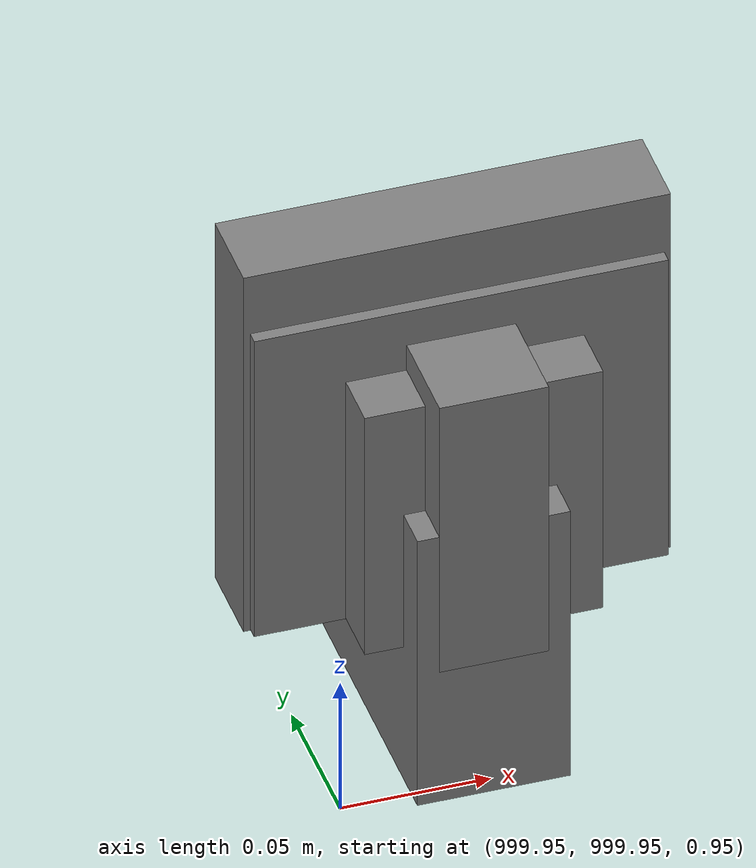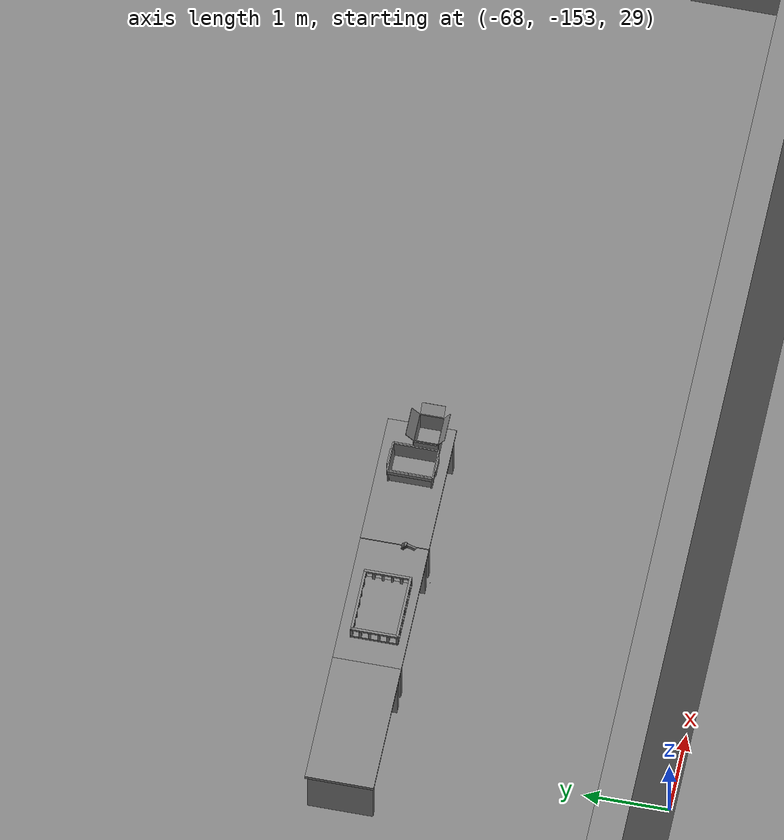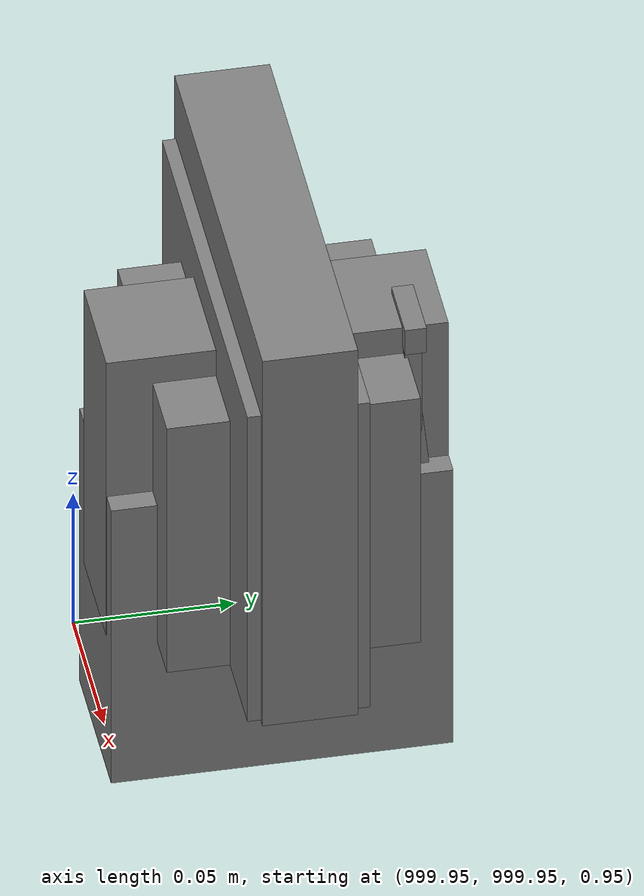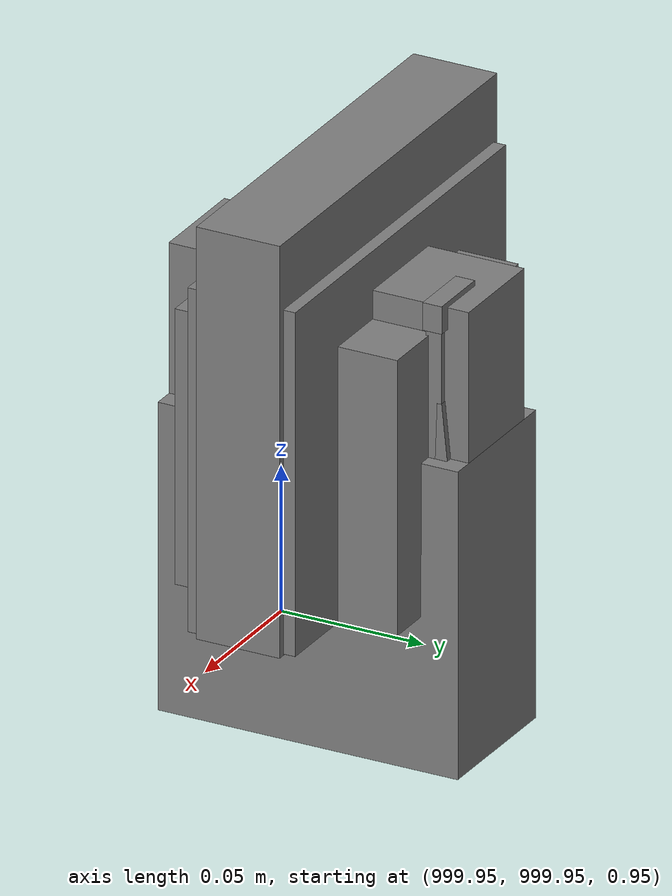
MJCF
<mujoco>
    <option gravity="0.000000000 0.000000000 -9.810000420" timestep="0.0049999999" integrator="implicitfast" density="1.225" viscosity="1.8000001e-05" noslip_iterations="10" iterations="100" sdf_iterations="50">
        <flag multiccd="disable"/>
    </option>
    <size memory="1000M"/>
    <compiler coordinate="local"/>
    <worldbody>
        <light cutoff="30" pos="0 1 1" dir="0 -1 -2"/>
        <light cutoff="30" pos="0 -1 1" dir="0 1 -2"/>
        <body pos="1000.000000000 1000.000000000 1.000000000" euler="0.000000000 0.000000000 180.000000000" name="openloong_gripper_2f85_fix_base_usda_cpu_fan">
            <geom contype="1" conaffinity="1" density="1000" type="box" material="" rgba="0.500000000 0.500000000 0.500000000 1.000000000" solimp="0.899999976 0.949999988 0.001000000" friction="1.000000000 0.005000000 0.000100000" solref="0.020000000 1.000000000" margin="0" condim="3" group="0" pos="0.000000000 0.000000000 0.070034981" quat="0.000000000 0.000000000 0.000000000 1.000000000" size="0.070700005 0.014699999 0.070700005" name="openloong_gripper_2f85_fix_base_usda_geom_AEAA2962_3066_4B24_A8D8_B6A27A1392D9"/>
            <freejoint name="openloong_gripper_2f85_fix_base_usda_cpu_fan_joint"/>
            <site size="0.005000000 0.005000000 0.005000000" rgba="0.500000000 0.500000000 0.500000000 1.000000000" pos="0.000000000 0.000000000 0.000000000" quat="0.999961913 0.008726535 0.000000000 0.000000000" group="0" type="sphere" name="openloong_gripper_2f85_fix_base_usda_cpu_fancsite"/>
        </body>
        <body pos="1000.000000000 1000.000000000 1.000000000" euler="0.000000000 0.000000000 180.000000000" name="openloong_gripper_2f85_fix_base_usda_wifi_box">
            <geom contype="1" conaffinity="1" density="1000" type="box" material="" rgba="0.500000000 0.500000000 0.500000000 1.000000000" solimp="0.899999976 0.949999988 0.001000000" friction="1.000000000 0.005000000 0.000100000" solref="0.020000000 1.000000000" margin="0" condim="3" group="0" pos="0.000000000 0.000000000 0.058978677" quat="0.000000000 0.000000047 0.000000000 1.000000000" size="0.068499997 0.018999999 0.059000000" name="openloong_gripper_2f85_fix_base_usda_geom_39F1E14E_01CA_4C0A_9606_C706BCAE9320"/>
            <freejoint name="openloong_gripper_2f85_fix_base_usda_wifi_box_joint"/>
            <site size="0.005000000 0.005000000 0.005000000" rgba="0.500000000 0.500000000 0.500000000 1.000000000" pos="0.000000000 0.000000000 0.000000000" quat="0.999961913 0.008726500 0.000000000 0.000000000" group="0" type="sphere" name="openloong_gripper_2f85_fix_base_usda_wifi_boxsite"/>
        </body>
        <body pos="-66.075706482 -148.897460938 31.170734406" euler="52.377407074 39.404956818 90.479499817" mocap="true" name="spotlight6_SpotLight"/>
        <body pos="-66.219573975 -148.827194214 31.164825439" euler="-105.156059265 -89.821121216 -69.543052673" mocap="true" name="spotlight5_SpotLight"/>
        <body pos="1000.000000000 1000.000000000 1.000000000" euler="0.000011953 0.000005123 -179.999984741" name="openloong_gripper_2f85_fix_base_usda_intel_box">
            <geom contype="1" conaffinity="1" density="1000" type="box" material="" rgba="0.500000000 0.500000000 0.500000000 1.000000000" solimp="0.899999976 0.949999988 0.001000000" friction="1.000000000 0.005000000 0.000100000" solref="0.020000000 1.000000000" margin="0" condim="3" group="0" pos="0.000000000 -0.000067139 0.000082284" quat="0.707106709 0.000000225 0.000000253 0.707106650" size="0.052800003 0.025300000 0.052800003" name="openloong_gripper_2f85_fix_base_usda_geom_42C0A19B_7726_4FD4_B844_3C72F244FEC9"/>
            <freejoint name="openloong_gripper_2f85_fix_base_usda_intel_box_joint"/>
            <site size="0.005000000 0.005000000 0.005000000" rgba="0.500000000 0.500000000 0.500000000 1.000000000" pos="0.000000000 0.000000000 0.000000000" quat="0.999961913 0.008726500 0.000000000 0.000000000" group="0" type="sphere" name="openloong_gripper_2f85_fix_base_usda_intel_boxsite"/>
        </body>
        <body pos="1000.000000000 1000.000000000 1.000000000" euler="0.000000000 0.000000000 180.000000000" name="openloong_gripper_2f85_fix_base_usda_battery_01">
            <geom contype="1" conaffinity="1" density="1000" type="box" material="" rgba="0.500000000 0.500000000 0.500000000 1.000000000" solimp="0.899999976 0.949999988 0.001000000" friction="1.000000000 0.005000000 0.000100000" solref="0.020000000 1.000000000" margin="0" condim="3" group="0" pos="-0.011123657 -0.041940309 0.101691343" quat="1.000000000 0.000000000 0.000000000 0.000000000" size="0.010800000 0.003375000 0.004725000" name="openloong_gripper_2f85_fix_base_usda_geom_4B6345F8_0EEA_4F60_BE66_A302058EB37A"/>
            <geom contype="1" conaffinity="1" density="1000" type="box" material="" rgba="0.500000000 0.500000000 0.500000000 1.000000000" solimp="0.899999976 0.949999988 0.001000000" friction="1.000000000 0.005000000 0.000100000" solref="0.020000000 1.000000000" margin="0" condim="3" group="0" pos="-0.010876465 -0.044247437 0.047066893" quat="0.998702705 -0.050920475 0.000000000 0.000000000" size="0.009450001 0.002700000 0.024975000" name="openloong_gripper_2f85_fix_base_usda_geom_DE1A7CF0_DDB3_4817_B1A0_E073452CD793"/>
            <geom contype="1" conaffinity="1" density="1000" type="box" material="" rgba="0.500000000 0.500000000 0.500000000 1.000000000" solimp="0.899999976 0.949999988 0.001000000" friction="1.000000000 0.005000000 0.000100000" solref="0.020000000 1.000000000" margin="0" condim="3" group="0" pos="-0.001235962 -0.000659180 0.047381196" quat="1.000000000 0.000000000 0.000000000 0.000000000" size="0.039420001 0.039150000 0.047250003" name="openloong_gripper_2f85_fix_base_usda_geom_224A7C0B_1631_4B19_B36C_9B2389AE4096"/>
            <geom contype="1" conaffinity="1" density="1000" type="box" material="" rgba="0.500000000 0.500000000 0.500000000 1.000000000" solimp="0.899999976 0.949999988 0.001000000" friction="1.000000000 0.005000000 0.000100000" solref="0.020000000 1.000000000" margin="0" condim="3" group="0" pos="-0.010876465 -0.039138794 0.009851727" quat="1.000000000 0.000000000 0.000000000 0.000000000" size="0.009450001 0.010800000 0.013500000" name="openloong_gripper_2f85_fix_base_usda_geom_5DC6E8D3_EB76_4D78_8E5E_C4A20B44626B"/>
            <geom contype="1" conaffinity="1" density="1000" type="box" material="" rgba="0.500000000 0.500000000 0.500000000 1.000000000" solimp="0.899999976 0.949999988 0.001000000" friction="1.000000000 0.005000000 0.000100000" solref="0.020000000 1.000000000" margin="0" condim="3" group="0" pos="-0.010876465 -0.041528322 0.071508206" quat="1.000000000 0.000000000 0.000000000 0.000000000" size="0.009450001 0.002700000 0.027000001" name="openloong_gripper_2f85_fix_base_usda_geom_2F4AA424_0D6F_4008_ADF2_18C608F9C452"/>
            <freejoint name="openloong_gripper_2f85_fix_base_usda_battery_01_joint"/>
            <site size="0.005000000 0.005000000 0.005000000" rgba="0.500000000 0.500000000 0.500000000 1.000000000" pos="0.000000000 0.000000000 0.000000000" quat="0.999961913 0.008726500 0.000000000 0.000000000" group="0" type="sphere" name="openloong_gripper_2f85_fix_base_usda_battery_01site"/>
        </body>
        <body pos="1000.000000000 999.999938965 1.000000000" euler="0.000000000 0.000000000 180.000000000" name="openloong_gripper_2f85_fix_base_usda_intelcore_i5">
            <geom contype="1" conaffinity="1" density="1000" type="box" material="" rgba="0.500000000 0.500000000 0.500000000 1.000000000" solimp="0.899999976 0.949999988 0.001000000" friction="1.000000000 0.005000000 0.000100000" solref="0.020000000 1.000000000" margin="0" condim="3" group="0" pos="0.000000000 0.000000000 0.051722717" quat="0.707106709 0.000000000 0.000000000 -0.707106769" size="0.052800000 0.018080002 0.052800000" name="openloong_gripper_2f85_fix_base_usda_geom_EDA45346_DC73_4B37_B74F_AD1D7DC7AF8F"/>
            <freejoint name="openloong_gripper_2f85_fix_base_usda_intelcore_i5_joint"/>
            <site size="0.005000000 0.005000000 0.005000000" rgba="0.500000000 0.500000000 0.500000000 1.000000000" pos="0.000000000 0.000000000 0.000000000" quat="0.999961913 0.008726534 0.000000000 0.000000000" group="0" type="sphere" name="openloong_gripper_2f85_fix_base_usda_intelcore_i5site"/>
        </body>
        <body pos="-66.315567017 -149.617492676 31.170827866" euler="112.500297546 74.798698425 141.634353638" mocap="true" name="spotlight1_SpotLight"/>
        <body pos="-64.866622925 -149.383972168 30.183746338" euler="89.999984741 89.999946594 0.000000000" name="openloong_gripper_2f85_fix_base_usda_bluebox_01">
            <geom contype="1" conaffinity="1" density="1000" type="box" material="" rgba="0.500000000 0.500000000 0.500000000 1.000000000" solimp="0.899999976 0.949999988 0.001000000" friction="1.000000000 0.005000000 0.000100000" solref="0.020000000 1.000000000" margin="0" condim="3" group="0" pos="0.276580811 0.187225342 0.000068665" quat="0.707106948 0.000077471 0.707106352 0.000077486" size="0.100000001 0.057999998 0.010000000" name="openloong_gripper_2f85_fix_base_usda_geom_2A56BBB1_4AA7_4764_993D_03058DB53950"/>
            <geom contype="1" conaffinity="1" density="1000" type="box" material="" rgba="0.500000000 0.500000000 0.500000000 1.000000000" solimp="0.899999976 0.949999988 0.001000000" friction="1.000000000 0.005000000 0.000100000" solref="0.020000000 1.000000000" margin="0" condim="3" group="0" pos="0.000000000 0.002883911 0.000000000" quat="0.999999881 0.000000000 0.000000000 0.000000000" size="0.254000008 0.003000000 0.172000006" name="openloong_gripper_2f85_fix_base_usda_geom_1625B3FE_16E5_4D57_889F_8C1627BFFBC0"/>
            <geom contype="1" conaffinity="1" density="1000" type="box" material="" rgba="0.500000000 0.500000000 0.500000000 1.000000000" solimp="0.899999976 0.949999988 0.001000000" friction="1.000000000 0.005000000 0.000100000" solref="0.020000000 1.000000000" margin="0" condim="3" group="0" pos="0.000000000 0.124874115 0.173484802" quat="0.999796331 0.020176515 -0.000000015 0.000000030" size="0.259999990 0.119999997 0.007000000" name="openloong_gripper_2f85_fix_base_usda_geom_683AE970_979E_4886_983B_89150D97D4CB"/>
            <geom contype="1" conaffinity="1" density="1000" type="box" material="" rgba="0.500000000 0.500000000 0.500000000 1.000000000" solimp="0.899999976 0.949999988 0.001000000" friction="1.000000000 0.005000000 0.000100000" solref="0.020000000 1.000000000" margin="0" condim="3" group="0" pos="0.000000000 0.124874115 -0.173469543" quat="0.999796331 -0.020176545 -0.000000015 0.000000000" size="0.259999990 0.119999997 0.007000000" name="openloong_gripper_2f85_fix_base_usda_geom_E2E0FD39_8114_461D_A114_99D3ACC81BCA"/>
            <geom contype="1" conaffinity="1" density="1000" type="box" material="" rgba="0.500000000 0.500000000 0.500000000 1.000000000" solimp="0.899999976 0.949999988 0.001000000" friction="1.000000000 0.005000000 0.000100000" solref="0.020000000 1.000000000" margin="0" condim="3" group="0" pos="0.000000000 0.214008331 0.188980103" quat="0.999912977 0.013176724 0.000000015 0.000000000" size="0.259999990 0.029999999 0.012500000" name="openloong_gripper_2f85_fix_base_usda_geom_2D02F53F_656C_446F_BF7B_6D173EBE2D99"/>
            <geom contype="1" conaffinity="1" density="1000" type="box" material="" rgba="0.500000000 0.500000000 0.500000000 1.000000000" solimp="0.899999976 0.949999988 0.001000000" friction="1.000000000 0.005000000 0.000100000" solref="0.020000000 1.000000000" margin="0" condim="3" group="0" pos="-0.258361816 0.125289917 0.001876831" quat="0.702796936 -0.020792112 0.710783124 0.020769298" size="0.189999998 0.119999997 0.009000000" name="openloong_gripper_2f85_fix_base_usda_geom_6F1AAC61_C40D_416A_AC44_3C77C8B4CAFD"/>
            <geom contype="1" conaffinity="1" density="1000" type="box" material="" rgba="0.500000000 0.500000000 0.500000000 1.000000000" solimp="0.899999976 0.949999988 0.001000000" friction="1.000000000 0.005000000 0.000100000" solref="0.020000000 1.000000000" margin="0" condim="3" group="0" pos="0.000000000 0.214008331 -0.188980103" quat="0.999912977 -0.013176769 0.000000030 0.000000015" size="0.259999990 0.029999999 0.012500000" name="openloong_gripper_2f85_fix_base_usda_geom_96636C5C_1A9C_46F4_B5A7_0A5BBDD83868"/>
            <geom contype="1" conaffinity="1" density="1000" type="box" material="" rgba="0.500000000 0.500000000 0.500000000 1.000000000" solimp="0.899999976 0.949999988 0.001000000" friction="1.000000000 0.005000000 0.000100000" solref="0.020000000 1.000000000" margin="0" condim="3" group="0" pos="-0.276611328 0.187225342 0.000068665" quat="0.707106650 0.000077441 0.707106709 0.000077456" size="0.100000001 0.057999998 0.010000000" name="openloong_gripper_2f85_fix_base_usda_geom_01B7DEAA_A2A1_43B9_9B20_8809113D89C2"/>
            <geom contype="1" conaffinity="1" density="1000" type="box" material="" rgba="0.500000000 0.500000000 0.500000000 1.000000000" solimp="0.899999976 0.949999988 0.001000000" friction="1.000000000 0.005000000 0.000100000" solref="0.020000000 1.000000000" margin="0" condim="3" group="0" pos="0.258331299 0.125289917 0.001876831" quat="0.702851415 0.018856421 0.710823774 -0.019329369" size="0.189999998 0.119999997 0.009000000" name="openloong_gripper_2f85_fix_base_usda_geom_A42E2215_638E_43FD_A9A0_073AB813B6E4"/>
            <freejoint name="openloong_gripper_2f85_fix_base_usda_bluebox_01_joint"/>
            <site size="0.005000000 0.005000000 0.005000000" rgba="0.500000000 0.500000000 0.500000000 1.000000000" pos="0.000000000 0.000000000 0.000000000" quat="0.999961913 0.008726534 0.000000000 0.000000000" group="0" type="sphere" name="openloong_gripper_2f85_fix_base_usda_bluebox_01site"/>
        </body>
        <body pos="-64.496299744 -149.491867065 30.235729218" euler="0.000000000 0.000000000 89.999946594" name="openloong_gripper_2f85_fix_base_usda_cardboardbox_01">
            <geom contype="1" conaffinity="1" density="1000" type="box" material="" rgba="0.500000000 0.500000000 0.500000000 1.000000000" solimp="0.899999976 0.949999988 0.001000000" friction="1.000000000 0.005000000 0.000100000" solref="0.020000000 1.000000000" margin="0" condim="3" group="0" pos="-0.003166199 -0.004086494 0.005052090" quat="1.000000000 0.000000000 0.000000000 0.000000000" size="0.142499998 0.177500010 0.005000000" name="openloong_gripper_2f85_fix_base_usda_geom_16CD8F4D_D97B_492C_AAF1_8918A6949270"/>
            <geom contype="1" conaffinity="1" density="1000" type="box" material="" rgba="0.500000000 0.500000000 0.500000000 1.000000000" solimp="0.899999976 0.949999988 0.001000000" friction="1.000000000 0.005000000 0.000100000" solref="0.020000000 1.000000000" margin="0" condim="3" group="0" pos="-0.003166199 0.170316696 0.150570869" quat="1.000000000 0.000000000 0.000000000 0.000000000" size="0.142499998 0.005000000 0.149999991" name="openloong_gripper_2f85_fix_base_usda_geom_A6F4914E_4750_41FD_BCA0_561910C3C0E6"/>
            <geom contype="1" conaffinity="1" density="1000" type="box" material="" rgba="0.500000000 0.500000000 0.500000000 1.000000000" solimp="0.899999976 0.949999988 0.001000000" friction="1.000000000 0.005000000 0.000100000" solref="0.020000000 1.000000000" margin="0" condim="3" group="0" pos="-0.147399902 -0.005307198 0.150570869" quat="1.000000000 0.000000000 0.000000000 0.000000000" size="0.005000000 0.177500010 0.149999991" name="openloong_gripper_2f85_fix_base_usda_geom_78492060_CDD1_430D_BE64_EBA7F0A054B4"/>
            <geom contype="1" conaffinity="1" density="1000" type="box" material="" rgba="0.500000000 0.500000000 0.500000000 1.000000000" solimp="0.899999976 0.949999988 0.001000000" friction="1.000000000 0.005000000 0.000100000" solref="0.020000000 1.000000000" margin="0" condim="3" group="0" pos="0.140275955 -0.005307198 0.150570869" quat="1.000000000 0.000000000 0.000000000 0.000000000" size="0.005000000 0.177500010 0.149999991" name="openloong_gripper_2f85_fix_base_usda_geom_B1969FE8_D4FC_430E_8DAA_24C0B33E2CA8"/>
            <geom contype="1" conaffinity="1" density="1000" type="box" material="" rgba="0.500000000 0.500000000 0.500000000 1.000000000" solimp="0.899999976 0.949999988 0.001000000" friction="1.000000000 0.005000000 0.000100000" solref="0.020000000 1.000000000" margin="0" condim="3" group="0" pos="-0.003166199 -0.181550980 0.150570869" quat="1.000000000 0.000000000 0.000000000 0.000000000" size="0.142499998 0.005000000 0.149999991" name="openloong_gripper_2f85_fix_base_usda_geom_2E30DF35_6331_4939_AE82_2C671519FCD9"/>
            <freejoint name="openloong_gripper_2f85_fix_base_usda_cardboardbox_01_joint"/>
            <site size="0.005000000 0.005000000 0.005000000" rgba="0.500000000 0.500000000 0.500000000 1.000000000" pos="0.000000000 0.000000000 0.000000000" quat="0.999961913 0.008726535 0.000000000 0.000000000" group="0" type="sphere" name="openloong_gripper_2f85_fix_base_usda_site_F831669A_6C00_40A1_8C0E_32069F06BB06"/>
            <body pos="0.139160156 -0.004048347 0.301930904" euler="-179.999954224 49.383502960 179.999954224" name="openloong_gripper_2f85_fix_base_usda_A1_006">
                <geom contype="1" conaffinity="1" density="1000" type="box" material="" rgba="0.500000000 0.500000000 0.500000000 1.000000000" solimp="0.899999976 0.949999988 0.001000000" friction="1.000000000 0.005000000 0.000100000" solref="0.020000000 1.000000000" margin="0" condim="3" group="0" pos="-0.071587563 0.000009537 0.001745224" quat="0.999999881 0.000000000 0.000000000 0.000000000" size="0.071249999 0.179999992 0.002500000" name="openloong_gripper_2f85_fix_base_usda_geom_1D1A6364_1D4F_4086_A062_926A201567FD"/>
                <joint armature="0" stiffness="0.07" damping="0.0099999998" axis="0.000000 1.000000 0.000000" type="hinge" name="openloong_gripper_2f85_fix_base_usda_A1_006"/>
            </body>
            <body pos="-0.145902634 -0.004086494 0.301938057" euler="-180.000000000 -60.000011444 -180.000000000" name="openloong_gripper_2f85_fix_base_usda_A2_006">
                <geom contype="1" conaffinity="1" density="1000" type="box" material="" rgba="0.500000000 0.500000000 0.500000000 1.000000000" solimp="0.899999976 0.949999988 0.001000000" friction="1.000000000 0.005000000 0.000100000" solref="0.020000000 1.000000000" margin="0" condim="3" group="0" pos="0.071268082 0.000009537 0.002717972" quat="0.000002921 0.000000000 -0.000000030 0.999999881" size="0.071249999 0.179999992 0.002500000" name="openloong_gripper_2f85_fix_base_usda_geom_58BF11ED_53C8_42DB_B405_E964A3439F28"/>
                <joint armature="0" stiffness="0.07" damping="0.0099999998" axis="0.000000 1.000000 0.000000" type="hinge" name="openloong_gripper_2f85_fix_base_usda_A2_006"/>
            </body>
            <body pos="-0.003385544 0.175991058 0.301930904" euler="-125.858116150 -0.000004561 0.000002331" name="openloong_gripper_2f85_fix_base_usda_B2_006">
                <geom contype="1" conaffinity="1" density="1000" type="box" material="" rgba="0.500000000 0.500000000 0.500000000 1.000000000" solimp="0.899999976 0.949999988 0.001000000" friction="1.000000000 0.005000000 0.000100000" solref="0.020000000 1.000000000" margin="0" condim="3" group="0" pos="0.000009537 -0.070939064 -0.002470016" quat="0.999614120 0.027776197 -0.000000015 0.000000030" size="0.137500003 0.064999998 0.005000000" name="openloong_gripper_2f85_fix_base_usda_geom_39F63B91_4435_4EEF_BC7E_1E439F223990"/>
                <joint armature="0" stiffness="0.07" damping="0.0099999998" axis="1.000000 0.000000 0.000000" type="hinge" name="openloong_gripper_2f85_fix_base_usda_B2_006"/>
            </body>
            <body pos="-0.003385544 -0.184140205 0.301938057" euler="147.805557251 0.000000000 0.000000000" name="openloong_gripper_2f85_fix_base_usda_B1_006">
                <geom contype="1" conaffinity="1" density="1000" type="box" material="" rgba="0.500000000 0.500000000 0.500000000 1.000000000" solimp="0.899999976 0.949999988 0.001000000" friction="1.000000000 0.005000000 0.000100000" solref="0.020000000 1.000000000" margin="0" condim="3" group="0" pos="-0.000028610 0.070202351 -0.002703667" quat="0.999614179 -0.027776167 0.000000000 0.000000000" size="0.137500003 0.064999998 0.005000000" name="openloong_gripper_2f85_fix_base_usda_geom_1B836FA5_D350_491D_BBB8_072ECFDF8E85"/>
                <joint armature="0" stiffness="0.07" damping="0.0099999998" axis="1.000000 0.000000 0.000000" type="hinge" name="openloong_gripper_2f85_fix_base_usda_B1_006"/>
            </body>
        </body>
        <body pos="-65.882858276 -149.481979370 30.229999542" euler="-64.487716675 0.000000000 0.000000000" name="openloong_gripper_2f85_fix_base_usda_Barcode">
            <geom contype="1" conaffinity="1" density="1000" type="box" material="" rgba="0.500000000 0.500000000 0.500000000 1.000000000" solimp="0.899999976 0.949999988 0.001000000" friction="1.000000000 0.005000000 0.000100000" solref="0.020000000 1.000000000" margin="0" condim="3" group="0" pos="0.000000000 0.013038635 0.001419067" quat="0.000000000 0.000000000 0.000000000 1.000000119" size="0.034000002 0.010000000 0.017999999" name="openloong_gripper_2f85_fix_base_usda_geom_31C5ED2E_AD7F_408F_B919_89B33418E9EE"/>
            <geom contype="1" conaffinity="1" density="1000" type="box" material="" rgba="0.500000000 0.500000000 0.500000000 1.000000000" solimp="0.899999976 0.949999988 0.001000000" friction="1.000000000 0.005000000 0.000100000" solref="0.020000000 1.000000000" margin="0" condim="3" group="0" pos="0.000000000 -0.035301208 -0.007095337" quat="0.000000000 0.000000000 -0.043619365 0.999048233" size="0.028999999 0.010000000 0.020000000" name="openloong_gripper_2f85_fix_base_usda_geom_8D0B0C66_22C0_492F_97F0_98D48E202C14"/>
            <geom contype="1" conaffinity="1" density="1000" type="box" material="" rgba="0.500000000 0.500000000 0.500000000 1.000000000" solimp="0.899999976 0.949999988 0.001000000" friction="1.000000000 0.005000000 0.000100000" solref="0.020000000 1.000000000" margin="0" condim="3" group="0" pos="0.000000000 -0.043411255 -0.011749268" quat="0.922262907 0.386563420 0.000000000 0.000000000" size="0.026000001 0.010000000 0.020000000" name="openloong_gripper_2f85_fix_base_usda_geom_A63964AD_CCA7_495F_8826_F3D099E153F2"/>
            <geom contype="1" conaffinity="1" density="1000" type="box" material="" rgba="0.500000000 0.500000000 0.500000000 1.000000000" solimp="0.899999976 0.949999988 0.001000000" friction="1.000000000 0.005000000 0.000100000" solref="0.020000000 1.000000000" margin="0" condim="3" group="0" pos="0.000000000 -0.016967773 -0.031860352" quat="0.000000000 0.000000000 0.000000000 1.000000119" size="0.008000000 0.010000000 0.013000000" name="openloong_gripper_2f85_fix_base_usda_geom_94054FB3_8FCB_4D57_94B0_55D93E023383"/>
            <geom contype="1" conaffinity="1" density="1000" type="box" material="" rgba="0.500000000 0.500000000 0.500000000 1.000000000" solimp="0.899999976 0.949999988 0.001000000" friction="1.000000000 0.005000000 0.000100000" solref="0.020000000 1.000000000" margin="0" condim="3" group="0" pos="0.000000000 -0.001869202 0.000312805" quat="0.953716993 0.300705761 0.000000000 0.000000000" size="0.032000002 0.010000000 0.018999999" name="openloong_gripper_2f85_fix_base_usda_geom_0FFD0607_042D_4B7F_96BA_076404EC5395"/>
            <geom contype="1" conaffinity="1" density="1000" type="box" material="" rgba="0.500000000 0.500000000 0.500000000 1.000000000" solimp="0.899999976 0.949999988 0.001000000" friction="1.000000000 0.005000000 0.000100000" solref="0.020000000 1.000000000" margin="0" condim="3" group="0" pos="0.000000000 -0.019531250 -0.003173828" quat="0.953716993 0.300705761 0.000000000 0.000000000" size="0.030999999 0.010000000 0.020000000" name="openloong_gripper_2f85_fix_base_usda_geom_15B5B912_A492_4F6D_9572_284DF2FE7577"/>
            <geom contype="1" conaffinity="1" density="1000" type="box" material="" rgba="0.500000000 0.500000000 0.500000000 1.000000000" solimp="0.899999976 0.949999988 0.001000000" friction="1.000000000 0.005000000 0.000100000" solref="0.020000000 1.000000000" margin="0" condim="3" group="0" pos="0.000000000 -0.035301208 -0.007095337" quat="0.953716993 0.300705761 0.000000000 0.000000000" size="0.028999999 0.010000000 0.020000000" name="openloong_gripper_2f85_fix_base_usda_geom_2160EB00_59B2_4A51_BCCB_1E1E40B0C62E"/>
            <geom contype="1" conaffinity="1" density="1000" type="box" material="" rgba="0.500000000 0.500000000 0.500000000 1.000000000" solimp="0.899999976 0.949999988 0.001000000" friction="1.000000000 0.005000000 0.000100000" solref="0.020000000 1.000000000" margin="0" condim="3" group="0" pos="0.000000000 -0.042617798 -0.071121216" quat="0.000000000 0.000000000 0.000000000 1.000000119" size="0.013000000 0.021000000 0.059999999" name="openloong_gripper_2f85_fix_base_usda_geom_45AD8C1D_DCD9_4C90_BDE0_2FB4BEE3664C"/>
            <freejoint name="openloong_gripper_2f85_fix_base_usda_Barcode_joint"/>
            <site size="0.005000000 0.005000000 0.005000000" rgba="0.500000000 0.500000000 0.500000000 1.000000000" pos="0.000000000 0.000000000 0.000000000" quat="1.000000000 0.000000000 0.000000000 0.000000000" group="0" type="sphere" name="openloong_gripper_2f85_fix_base_usda_Barcode_site"/>
        </body>
        <body pos="-66.745018005 -149.392349243 30.184000015" euler="0.000000000 0.000000000 89.999946594" name="[22329946433494]_Basket_01">
            <geom contype="1" conaffinity="1" density="1000" type="box" material="" rgba="0.500000000 0.500000000 0.500000000 1.000000000" solimp="0.899999976 0.949999988 0.001000000" friction="1.000000000 0.005000000 0.000100000" solref="0.020000000 1.000000000" margin="0" condim="3" group="0" pos="-0.052425385 0.389207840 0.089787483" quat="0.707107008 0.000000000 0.000000000 0.707106411" size="0.014249999 0.014249999 0.059999999" name="[22329946433494]_geom_842D75C2_5461_40E3_BF13_FDD40076F2EA"/>
            <geom contype="1" conaffinity="1" density="1000" type="box" material="" rgba="0.500000000 0.500000000 0.500000000 1.000000000" solimp="0.899999976 0.949999988 0.001000000" friction="1.000000000 0.005000000 0.000100000" solref="0.020000000 1.000000000" margin="0" condim="3" group="0" pos="0.264015198 -0.133043289 0.089787483" quat="0.707107008 0.000000000 0.000000000 0.707106411" size="0.014249999 0.014249999 0.059999999" name="[22329946433494]_geom_A889A787_EDCC_487D_846C_2F010946E415"/>
            <geom contype="1" conaffinity="1" density="1000" type="box" material="" rgba="0.500000000 0.500000000 0.500000000 1.000000000" solimp="0.899999976 0.949999988 0.001000000" friction="1.000000000 0.005000000 0.000100000" solref="0.020000000 1.000000000" margin="0" condim="3" group="0" pos="-0.264015198 -0.265548706 0.089793205" quat="0.707107008 0.000000000 0.000000000 0.707106411" size="0.014249999 0.014249999 0.059999999" name="[22329946433494]_geom_C74E2440_7FCF_42BD_9E48_32BA3F46A793"/>
            <geom contype="1" conaffinity="1" density="1000" type="box" material="" rgba="0.500000000 0.500000000 0.500000000 1.000000000" solimp="0.899999976 0.949999988 0.001000000" friction="1.000000000 0.005000000 0.000100000" solref="0.020000000 1.000000000" margin="0" condim="3" group="0" pos="-0.160263062 -0.389322281 0.089793205" quat="0.707107008 0.000000000 0.000000000 0.707106411" size="0.014249999 0.014249999 0.059999999" name="[22329946433494]_geom_A1B6D614_D892_42DD_8920_968C37A65B6E"/>
            <geom contype="1" conaffinity="1" density="1000" type="box" material="" rgba="0.500000000 0.500000000 0.500000000 1.000000000" solimp="0.899999976 0.949999988 0.001000000" friction="1.000000000 0.005000000 0.000100000" solref="0.020000000 1.000000000" margin="0" condim="3" group="0" pos="0.162265778 -0.389322281 0.089787483" quat="0.707107008 0.000000000 0.000000000 0.707106411" size="0.014249999 0.014249999 0.059999999" name="[22329946433494]_geom_5CD3F844_D02B_457E_8373_196002456B41"/>
            <geom contype="1" conaffinity="1" density="1000" type="box" material="" rgba="0.500000000 0.500000000 0.500000000 1.000000000" solimp="0.899999976 0.949999988 0.001000000" friction="1.000000000 0.005000000 0.000100000" solref="0.020000000 1.000000000" margin="0" condim="3" group="0" pos="0.264015198 0.389207840 0.089787483" quat="0.707107008 0.000000000 0.000000000 0.707106411" size="0.014249999 0.014249999 0.059999999" name="[22329946433494]_geom_0D243ADC_725C_4775_AB0E_3C14144319D7"/>
            <geom contype="1" conaffinity="1" density="1000" type="box" material="" rgba="0.500000000 0.500000000 0.500000000 1.000000000" solimp="0.899999976 0.949999988 0.001000000" friction="1.000000000 0.005000000 0.000100000" solref="0.020000000 1.000000000" margin="0" condim="3" group="0" pos="-0.264015198 -0.133043289 0.089793205" quat="0.707107008 0.000000000 0.000000000 0.707106411" size="0.014249999 0.014249999 0.059999999" name="[22329946433494]_geom_1F538244_6421_4A64_BAC0_AFF5CDDD8ABB"/>
            <geom contype="1" conaffinity="1" density="1000" type="box" material="" rgba="0.500000000 0.500000000 0.500000000 1.000000000" solimp="0.899999976 0.949999988 0.001000000" friction="1.000000000 0.005000000 0.000100000" solref="0.020000000 1.000000000" margin="0" condim="3" group="0" pos="-0.264026642 0.269256592 0.089793205" quat="0.707107008 0.000000000 0.000000000 0.707106411" size="0.014249999 0.014249999 0.059999999" name="[22329946433494]_geom_590BA201_63DF_4BAD_BF38_9AC68295825A"/>
            <geom contype="1" conaffinity="1" density="1000" type="box" material="" rgba="0.500000000 0.500000000 0.500000000 1.000000000" solimp="0.899999976 0.949999988 0.001000000" friction="1.000000000 0.005000000 0.000100000" solref="0.020000000 1.000000000" margin="0" condim="3" group="0" pos="0.054462433 0.389207840 0.089787483" quat="0.707107008 0.000000000 0.000000000 0.707106411" size="0.014249999 0.014249999 0.059999999" name="[22329946433494]_geom_E44CDE7C_800A_44CF_96AA_0C23EAA25948"/>
            <geom contype="1" conaffinity="1" density="1000" type="box" material="" rgba="0.500000000 0.500000000 0.500000000 1.000000000" solimp="0.899999976 0.949999988 0.001000000" friction="1.000000000 0.005000000 0.000100000" solref="0.020000000 1.000000000" margin="0" condim="3" group="0" pos="0.054462433 -0.389322281 0.089787483" quat="0.707107008 0.000000000 0.000000000 0.707106411" size="0.014249999 0.014249999 0.059999999" name="[22329946433494]_geom_99028630_215D_4454_920D_1D5EEC00E32F"/>
            <geom contype="1" conaffinity="1" density="1000" type="box" material="" rgba="0.500000000 0.500000000 0.500000000 1.000000000" solimp="0.899999976 0.949999988 0.001000000" friction="1.000000000 0.005000000 0.000100000" solref="0.020000000 1.000000000" margin="0" condim="3" group="0" pos="0.264015198 0.269256592 0.089793205" quat="0.707107008 0.000000000 0.000000000 0.707106411" size="0.014249999 0.014249999 0.059999999" name="[22329946433494]_geom_F468B29E_09F6_40D8_9204_584F9531EDAE"/>
            <geom contype="1" conaffinity="1" density="1000" type="box" material="" rgba="0.500000000 0.500000000 0.500000000 1.000000000" solimp="0.899999976 0.949999988 0.001000000" friction="1.000000000 0.005000000 0.000100000" solref="0.020000000 1.000000000" margin="0" condim="3" group="0" pos="0.264015198 -0.389322281 0.089787483" quat="0.707107008 0.000000000 0.000000000 0.707106411" size="0.014249999 0.014249999 0.059999999" name="[22329946433494]_geom_ED7009A9_7D84_4E2F_9A7A_422D4554555F"/>
            <geom contype="1" conaffinity="1" density="1000" type="box" material="" rgba="0.500000000 0.500000000 0.500000000 1.000000000" solimp="0.899999976 0.949999988 0.001000000" friction="1.000000000 0.005000000 0.000100000" solref="0.020000000 1.000000000" margin="0" condim="3" group="0" pos="0.000000000 0.000000000 0.015998840" quat="0.707107008 0.000000000 0.000000000 0.707106411" size="0.403499991 0.279000014 0.015750000" name="[22329946433494]_geom_A99FAA17_F6A1_4B84_AD7D_06B52E92D3D5"/>
            <geom contype="1" conaffinity="1" density="1000" type="box" material="" rgba="0.500000000 0.500000000 0.500000000 1.000000000" solimp="0.899999976 0.949999988 0.001000000" friction="1.000000000 0.005000000 0.000100000" solref="0.020000000 1.000000000" margin="0" condim="3" group="0" pos="0.000000000 -0.389476776 0.163619041" quat="0.707107008 0.000000000 0.000000000 0.707106411" size="0.015000000 0.277500004 0.015750000" name="[22329946433494]_geom_7FF98BE5_F92F_4F33_AA1D_E34074AE45CF"/>
            <geom contype="1" conaffinity="1" density="1000" type="box" material="" rgba="0.500000000 0.500000000 0.500000000 1.000000000" solimp="0.899999976 0.949999988 0.001000000" friction="1.000000000 0.005000000 0.000100000" solref="0.020000000 1.000000000" margin="0" condim="3" group="0" pos="0.162265778 0.389207840 0.089787483" quat="0.707107008 0.000000000 0.000000000 0.707106411" size="0.014249999 0.014249999 0.059999999" name="[22329946433494]_geom_A17F662C_6B80_4DA5_ABD4_9566D688C6F9"/>
            <geom contype="1" conaffinity="1" density="1000" type="box" material="" rgba="0.500000000 0.500000000 0.500000000 1.000000000" solimp="0.899999976 0.949999988 0.001000000" friction="1.000000000 0.005000000 0.000100000" solref="0.020000000 1.000000000" margin="0" condim="3" group="0" pos="0.000000000 0.389471054 0.163619041" quat="0.707107008 0.000000000 0.000000000 0.707106411" size="0.015000000 0.277500004 0.015750000" name="[22329946433494]_geom_AACF6773_1DCC_427E_BB6C_D06581CEDF24"/>
            <geom contype="1" conaffinity="1" density="1000" type="box" material="" rgba="0.500000000 0.500000000 0.500000000 1.000000000" solimp="0.899999976 0.949999988 0.001000000" friction="1.000000000 0.005000000 0.000100000" solref="0.020000000 1.000000000" margin="0" condim="3" group="0" pos="-0.263511658 0.000000000 0.163619041" quat="0.707107008 0.000000000 0.000000000 0.707106411" size="0.403499991 0.015000000 0.015750000" name="[22329946433494]_geom_7B27BEB3_67B3_4740_8256_BBC19FB5849D"/>
            <geom contype="1" conaffinity="1" density="1000" type="box" material="" rgba="0.500000000 0.500000000 0.500000000 1.000000000" solimp="0.899999976 0.949999988 0.001000000" friction="1.000000000 0.005000000 0.000100000" solref="0.020000000 1.000000000" margin="0" condim="3" group="0" pos="-0.264015198 0.141334534 0.089793205" quat="0.707107008 0.000000000 0.000000000 0.707106411" size="0.014249999 0.014249999 0.059999999" name="[22329946433494]_geom_B7A9B018_C0E8_4E13_9D41_FDF9D21C4F7F"/>
            <geom contype="1" conaffinity="1" density="1000" type="box" material="" rgba="0.500000000 0.500000000 0.500000000 1.000000000" solimp="0.899999976 0.949999988 0.001000000" friction="1.000000000 0.005000000 0.000100000" solref="0.020000000 1.000000000" margin="0" condim="3" group="0" pos="0.264015198 -0.265548706 0.089787483" quat="0.707107008 0.000000000 0.000000000 0.707106411" size="0.014249999 0.014249999 0.059999999" name="[22329946433494]_geom_9398F411_42A0_4A11_BBCB_98B7A7FD7887"/>
            <geom contype="1" conaffinity="1" density="1000" type="box" material="" rgba="0.500000000 0.500000000 0.500000000 1.000000000" solimp="0.899999976 0.949999988 0.001000000" friction="1.000000000 0.005000000 0.000100000" solref="0.020000000 1.000000000" margin="0" condim="3" group="0" pos="-0.160263062 0.389207840 0.089787483" quat="0.707107008 0.000000000 0.000000000 0.707106411" size="0.014249999 0.014249999 0.059999999" name="[22329946433494]_geom_A58D60FD_951D_43F2_A42B_8F7AE5ECF7A9"/>
            <geom contype="1" conaffinity="1" density="1000" type="box" material="" rgba="0.500000000 0.500000000 0.500000000 1.000000000" solimp="0.899999976 0.949999988 0.001000000" friction="1.000000000 0.005000000 0.000100000" solref="0.020000000 1.000000000" margin="0" condim="3" group="0" pos="-0.052425385 -0.389322281 0.089787483" quat="0.707107008 0.000000000 0.000000000 0.707106411" size="0.014249999 0.014249999 0.059999999" name="[22329946433494]_geom_9884AF5F_C7D6_4C7A_8905_6E2DA902CBF1"/>
            <geom contype="1" conaffinity="1" density="1000" type="box" material="" rgba="0.500000000 0.500000000 0.500000000 1.000000000" solimp="0.899999976 0.949999988 0.001000000" friction="1.000000000 0.005000000 0.000100000" solref="0.020000000 1.000000000" margin="0" condim="3" group="0" pos="-0.264026642 -0.389322281 0.089793205" quat="0.707107008 0.000000000 0.000000000 0.707106411" size="0.014249999 0.014249999 0.059999999" name="[22329946433494]_geom_E2A836E2_CEB5_4F4C_A218_620AD7406DFE"/>
            <geom contype="1" conaffinity="1" density="1000" type="box" material="" rgba="0.500000000 0.500000000 0.500000000 1.000000000" solimp="0.899999976 0.949999988 0.001000000" friction="1.000000000 0.005000000 0.000100000" solref="0.020000000 1.000000000" margin="0" condim="3" group="0" pos="0.264015198 0.141334534 0.089787483" quat="0.707107008 0.000000000 0.000000000 0.707106411" size="0.014249999 0.014249999 0.059999999" name="[22329946433494]_geom_EC183044_F36E_4DC2_92A9_3B1E3E6B4DBC"/>
            <geom contype="1" conaffinity="1" density="1000" type="box" material="" rgba="0.500000000 0.500000000 0.500000000 1.000000000" solimp="0.899999976 0.949999988 0.001000000" friction="1.000000000 0.005000000 0.000100000" solref="0.020000000 1.000000000" margin="0" condim="3" group="0" pos="-0.264015198 0.389207840 0.089793205" quat="0.707107008 0.000000000 0.000000000 0.707106411" size="0.014249999 0.014249999 0.059999999" name="[22329946433494]_geom_E0700281_C47E_4F2F_A26D_11109B08BD73"/>
            <geom contype="1" conaffinity="1" density="1000" type="box" material="" rgba="0.500000000 0.500000000 0.500000000 1.000000000" solimp="0.899999976 0.949999988 0.001000000" friction="1.000000000 0.005000000 0.000100000" solref="0.020000000 1.000000000" margin="0" condim="3" group="0" pos="0.264015198 0.004480362 0.089787483" quat="0.707107008 0.000000000 0.000000000 0.707106411" size="0.014249999 0.014249999 0.059999999" name="[22329946433494]_geom_3A70E140_AEC3_4FCB_B9CE_3248C00C8977"/>
            <geom contype="1" conaffinity="1" density="1000" type="box" material="" rgba="0.500000000 0.500000000 0.500000000 1.000000000" solimp="0.899999976 0.949999988 0.001000000" friction="1.000000000 0.005000000 0.000100000" solref="0.020000000 1.000000000" margin="0" condim="3" group="0" pos="0.263694763 -0.000011444 0.163619041" quat="0.707107008 0.000000000 0.000000000 0.707106411" size="0.403499991 0.015000000 0.015750000" name="[22329946433494]_geom_43566072_0C92_4CC8_A5DB_642CBD24F22B"/>
            <geom contype="1" conaffinity="1" density="1000" type="box" material="" rgba="0.500000000 0.500000000 0.500000000 1.000000000" solimp="0.899999976 0.949999988 0.001000000" friction="1.000000000 0.005000000 0.000100000" solref="0.020000000 1.000000000" margin="0" condim="3" group="0" pos="-0.264015198 0.004480362 0.089793205" quat="0.707107008 0.000000000 0.000000000 0.707106411" size="0.014249999 0.014249999 0.059999999" name="[22329946433494]_geom_52D604C5_6D27_4C5C_8D24_62869DF4598F"/>
            <freejoint name="[22329946433494]_joint_B3B95E21_A96B_48C9_8A84_41B8CCC4C7A0"/>
        </body>
        <body pos="0.000000000 0.000000000 0.000000000" euler="0.000000000 0.000000000 0.000000000" name="Static Objects_Static Objects">
            <geom contype="1" conaffinity="1" density="1000" type="box" material="" rgba="0.500000000 0.500000000 0.500000000 1.000000000" solimp="0.899999976 0.949999988 0.001000000" friction="1.000000000 0.005000000 0.000100000" solref="0.020000000 1.000000000" margin="0" condim="3" group="0" pos="-67.544113159 -149.365814209 29.727830887" quat="0.500000417 0.499999970 0.499999553 0.499999970" size="0.381000012 0.319999993 0.041000001" name="Static Objects_geom_C3072305_0F86_494C_B4B3_00C4FE932844"/>
            <geom contype="1" conaffinity="1" density="1000" type="box" material="" rgba="0.500000000 0.500000000 0.500000000 1.000000000" solimp="0.899999976 0.949999988 0.001000000" friction="1.000000000 0.005000000 0.000100000" solref="0.020000000 1.000000000" margin="0" condim="3" group="0" pos="-68.239501953 -149.365814209 30.086868286" quat="0.500000417 0.499999970 0.499999553 0.499999970" size="0.370999992 0.039500002 0.745000005" name="Static Objects_geom_DD5A26AB_E95F_4C7E_9030_710D1B2F2CEE"/>
            <geom contype="1" conaffinity="1" density="1000" type="box" material="" rgba="0.500000000 0.500000000 0.500000000 1.000000000" solimp="0.899999976 0.949999988 0.001000000" friction="1.000000000 0.005000000 0.000100000" solref="0.020000000 1.000000000" margin="0" condim="3" group="0" pos="-68.239501953 -149.365814209 30.147235870" quat="0.500000417 0.499999970 0.499999553 0.499999970" size="0.400000006 0.022000000 0.800000012" name="Static Objects_geom_069775AB_4634_44FC_9832_3DF6FEB61FAB"/>
            <geom contype="1" conaffinity="1" density="1000" type="box" material="" rgba="0.500000000 0.500000000 0.500000000 1.000000000" solimp="0.899999976 0.949999988 0.001000000" friction="1.000000000 0.005000000 0.000100000" solref="0.020000000 1.000000000" margin="0" condim="3" group="0" pos="-68.934890747 -149.365814209 29.727830887" quat="0.500000417 0.499999970 0.499999553 0.499999970" size="0.381000012 0.319999993 0.041000001" name="Static Objects_geom_AA6F7083_70BB_423F_B7C1_7D0AF1080ADE"/>
            <geom contype="1" conaffinity="1" density="1000" type="box" material="" rgba="0.500000000 0.500000000 0.500000000 1.000000000" solimp="0.899999976 0.949999988 0.001000000" friction="1.000000000 0.005000000 0.000100000" solref="0.020000000 1.000000000" margin="0" condim="3" group="0" pos="-68.239501953 -149.365814209 29.561563492" quat="0.500000417 0.499999970 0.499999553 0.499999970" size="0.020000000 0.022000000 0.660000026" name="Static Objects_geom_90A0FBE7_A4C8_4604_972F_64824582C245"/>
            <geom contype="1" conaffinity="1" density="1000" type="box" material="" rgba="0.500000000 0.500000000 0.500000000 1.000000000" solimp="0.899999976 0.949999988 0.001000000" friction="1.000000000 0.005000000 0.000100000" solref="0.020000000 1.000000000" margin="0" condim="3" group="0" pos="-65.945671082 -149.365814209 29.727830887" quat="0.500000417 0.499999970 0.499999553 0.499999970" size="0.381000012 0.319999993 0.041000001" name="Static Objects_geom_46158A70_97E9_420E_9474_AF8F6DF67263"/>
            <geom contype="1" conaffinity="1" density="1000" type="box" material="" rgba="0.500000000 0.500000000 0.500000000 1.000000000" solimp="0.899999976 0.949999988 0.001000000" friction="1.000000000 0.005000000 0.000100000" solref="0.020000000 1.000000000" margin="0" condim="3" group="0" pos="-66.641059875 -149.365814209 30.086868286" quat="0.500000417 0.499999970 0.499999553 0.499999970" size="0.370999992 0.039500002 0.745000005" name="Static Objects_geom_7968868D_149A_40C4_AF87_A18580CB66C1"/>
            <geom contype="1" conaffinity="1" density="1000" type="box" material="" rgba="0.500000000 0.500000000 0.500000000 1.000000000" solimp="0.899999976 0.949999988 0.001000000" friction="1.000000000 0.005000000 0.000100000" solref="0.020000000 1.000000000" margin="0" condim="3" group="0" pos="-66.641059875 -149.365814209 30.147235870" quat="0.500000417 0.499999970 0.499999553 0.499999970" size="0.400000006 0.022000000 0.800000012" name="Static Objects_geom_C172CE6A_FC20_4E0C_B1A4_F74805BE1AA3"/>
            <geom contype="1" conaffinity="1" density="1000" type="box" material="" rgba="0.500000000 0.500000000 0.500000000 1.000000000" solimp="0.899999976 0.949999988 0.001000000" friction="1.000000000 0.005000000 0.000100000" solref="0.020000000 1.000000000" margin="0" condim="3" group="0" pos="-67.336448669 -149.365814209 29.727830887" quat="0.500000417 0.499999970 0.499999553 0.499999970" size="0.381000012 0.319999993 0.041000001" name="Static Objects_geom_31664CF7_1A2C_4F66_800E_F3E2A05D6FC5"/>
            <geom contype="1" conaffinity="1" density="1000" type="box" material="" rgba="0.500000000 0.500000000 0.500000000 1.000000000" solimp="0.899999976 0.949999988 0.001000000" friction="1.000000000 0.005000000 0.000100000" solref="0.020000000 1.000000000" margin="0" condim="3" group="0" pos="-66.641059875 -149.365814209 29.561563492" quat="0.500000417 0.499999970 0.499999553 0.499999970" size="0.020000000 0.022000000 0.660000026" name="Static Objects_geom_FE6BBE85_7C13_45B7_BB11_5F1A9D7CD4DE"/>
            <geom contype="1" conaffinity="1" density="1000" type="box" material="" rgba="0.500000000 0.500000000 0.500000000 1.000000000" solimp="0.899999976 0.949999988 0.001000000" friction="1.000000000 0.005000000 0.000100000" solref="0.020000000 1.000000000" margin="0" condim="3" group="0" pos="-64.338577271 -149.365814209 29.727830887" quat="0.500000417 0.499999970 0.499999553 0.499999970" size="0.381000012 0.319999993 0.041000001" name="Static Objects_geom_0EC74371_6D08_45FA_BB89_F88FA78798AD"/>
            <geom contype="1" conaffinity="1" density="1000" type="box" material="" rgba="0.500000000 0.500000000 0.500000000 1.000000000" solimp="0.899999976 0.949999988 0.001000000" friction="1.000000000 0.005000000 0.000100000" solref="0.020000000 1.000000000" margin="0" condim="3" group="0" pos="-65.033966064 -149.365814209 30.086868286" quat="0.500000417 0.499999970 0.499999553 0.499999970" size="0.370999992 0.039500002 0.745000005" name="Static Objects_geom_1D8BF838_0D04_4ECB_B8CC_D5FF3C351966"/>
            <geom contype="1" conaffinity="1" density="1000" type="box" material="" rgba="0.500000000 0.500000000 0.500000000 1.000000000" solimp="0.899999976 0.949999988 0.001000000" friction="1.000000000 0.005000000 0.000100000" solref="0.020000000 1.000000000" margin="0" condim="3" group="0" pos="-65.033966064 -149.365814209 30.147235870" quat="0.500000417 0.499999970 0.499999553 0.499999970" size="0.400000006 0.022000000 0.800000012" name="Static Objects_geom_06CA5C45_CF6D_4D87_BBEB_08C4EC12E58A"/>
            <geom contype="1" conaffinity="1" density="1000" type="box" material="" rgba="0.500000000 0.500000000 0.500000000 1.000000000" solimp="0.899999976 0.949999988 0.001000000" friction="1.000000000 0.005000000 0.000100000" solref="0.020000000 1.000000000" margin="0" condim="3" group="0" pos="-65.729354858 -149.365814209 29.727830887" quat="0.500000417 0.499999970 0.499999553 0.499999970" size="0.381000012 0.319999993 0.041000001" name="Static Objects_geom_C869229A_1715_4122_8D24_0A67D9897D70"/>
            <geom contype="1" conaffinity="1" density="1000" type="box" material="" rgba="0.500000000 0.500000000 0.500000000 1.000000000" solimp="0.899999976 0.949999988 0.001000000" friction="1.000000000 0.005000000 0.000100000" solref="0.020000000 1.000000000" margin="0" condim="3" group="0" pos="-65.033966064 -149.365814209 29.561563492" quat="0.500000417 0.499999970 0.499999553 0.499999970" size="0.020000000 0.022000000 0.660000026" name="Static Objects_geom_7D99F70C_1466_4966_AE68_2839918F584B"/>
            <geom contype="1" conaffinity="1" density="1000" type="box" material="" rgba="0.500000000 0.500000000 0.500000000 1.000000000" solimp="0.899999976 0.949999988 0.001000000" friction="1.000000000 0.005000000 0.000100000" solref="0.020000000 1.000000000" margin="0" condim="3" group="0" pos="-61.754566193 -137.853729248 33.906845093" quat="0.707107067 0.000000000 0.000000000 0.707106471" size="0.759999990 0.759999990 4.500000000" name="Static Objects_geom_8A7A6694_04AA_4AB3_BDBC_B4A9414C182A"/>
            <geom contype="1" conaffinity="1" density="1000" type="box" material="" rgba="0.500000000 0.500000000 0.500000000 1.000000000" solimp="0.899999976 0.949999988 0.001000000" friction="1.000000000 0.005000000 0.000100000" solref="0.020000000 1.000000000" margin="0" condim="3" group="0" pos="-57.511135101 -144.927108765 31.707921982" quat="1.000000000 0.000000000 0.000000000 0.000000000" size="0.200000003 8.000000000 2.299999952" name="Static Objects_geom_51FECE12_F663_4673_94A0_050E7264B74E"/>
            <geom contype="1" conaffinity="1" density="1000" type="box" material="" rgba="0.500000000 0.500000000 0.500000000 1.000000000" solimp="0.899999976 0.949999988 0.001000000" friction="1.000000000 0.005000000 0.000100000" solref="0.020000000 1.000000000" margin="0" condim="3" group="0" pos="-80.517646790 -157.574050903 31.688196182" quat="0.707107067 0.000000000 0.000000000 0.707106471" size="0.600000024 0.600000024 2.299999952" name="Static Objects_geom_096A51D6_DFB4_4472_9BC4_43F986900038"/>
            <geom contype="1" conaffinity="1" density="1000" type="box" material="" rgba="0.500000000 0.500000000 0.500000000 1.000000000" solimp="0.899999976 0.949999988 0.001000000" friction="1.000000000 0.005000000 0.000100000" solref="0.020000000 1.000000000" margin="0" condim="3" group="0" pos="-80.711044312 -147.414932251 31.666158676" quat="1.000000000 0.000000000 0.000000000 0.000000000" size="0.200000003 10.000000000 2.299999952" name="Static Objects_geom_8D45E934_71E4_4124_8A62_6B8AC54753E3"/>
            <geom contype="1" conaffinity="1" density="1000" type="box" material="" rgba="0.500000000 0.500000000 0.500000000 1.000000000" solimp="0.899999976 0.949999988 0.001000000" friction="1.000000000 0.005000000 0.000100000" solref="0.020000000 1.000000000" margin="0" condim="3" group="0" pos="-57.687217712 -137.434692383 31.688196182" quat="0.707107067 0.000000000 0.000000000 0.707106471" size="0.600000024 0.600000024 2.299999952" name="Static Objects_geom_75058281_2F2E_4F94_A2AE_1C948B3B7A1A"/>
            <geom contype="1" conaffinity="1" density="1000" type="box" material="" rgba="0.500000000 0.500000000 0.500000000 1.000000000" solimp="0.899999976 0.949999988 0.001000000" friction="1.000000000 0.005000000 0.000100000" solref="0.020000000 1.000000000" margin="0" condim="3" group="0" pos="-69.537033081 -140.263229370 31.714921951" quat="0.707107067 0.000000000 0.000000000 0.707106471" size="0.759999990 4.500000000 2.299999952" name="Static Objects_geom_9F2B66EC_433E_471A_833C_58276A6A6052"/>
            <geom contype="1" conaffinity="1" density="1000" type="box" material="" rgba="0.500000000 0.500000000 0.500000000 1.000000000" solimp="0.899999976 0.949999988 0.001000000" friction="1.000000000 0.005000000 0.000100000" solref="0.020000000 1.000000000" margin="0" condim="3" group="0" pos="-80.073638916 -137.853713989 33.906845093" quat="0.707107067 0.000000000 0.000000000 0.707106471" size="0.759999990 0.759999990 4.500000000" name="Static Objects_geom_136F8EC6_B867_441E_9D78_1E0932026239"/>
            <geom contype="1" conaffinity="1" density="1000" type="box" material="" rgba="0.500000000 0.500000000 0.500000000 1.000000000" solimp="0.899999976 0.949999988 0.001000000" friction="1.000000000 0.005000000 0.000100000" solref="0.020000000 1.000000000" margin="0" condim="3" group="0" pos="-73.406707764 -155.734664917 31.707921982" quat="1.000000000 0.000000000 0.000000000 0.000000000" size="0.200000003 3.000000000 2.299999952" name="Static Objects_geom_816874AE_6ABA_4E5A_8378_48BFF203C9B4"/>
            <geom contype="1" conaffinity="1" density="1000" type="box" material="" rgba="0.500000000 0.500000000 0.500000000 1.000000000" solimp="0.899999976 0.949999988 0.001000000" friction="1.000000000 0.005000000 0.000100000" solref="0.020000000 1.000000000" margin="0" condim="3" group="0" pos="-68.497543335 -137.448257446 31.707921982" quat="0.707107067 0.000000000 0.000000000 0.707106471" size="0.200000003 14.000000000 2.299999952" name="Static Objects_geom_DA552B63_826F_46F9_AE54_F9AB0D7080EF"/>
            <geom contype="1" conaffinity="1" density="1000" type="cylinder" material="" rgba="0.500000000 0.500000000 0.500000000 1.000000000" solimp="0.899999976 0.949999988 0.001000000" friction="1.000000000 0.005000000 0.000100000" solref="0.020000000 1.000000000" margin="0" condim="3" group="0" pos="-68.868522644 -142.134506226 31.711090088" quat="0.707107067 0.000000000 0.000000000 0.707106471" size="0.509999990 2.299999952 1.000000000" name="Static Objects_geom_F6EE9F5A_49D1_4DE1_8308_8E50C2E26146"/>
            <geom contype="1" conaffinity="1" density="1000" type="plane" material="" rgba="0.500000000 0.500000000 0.500000000 1.000000000" solimp="0.899999976 0.949999988 0.001000000" friction="1.000000000 0.005000000 0.000100000" solref="0.020000000 1.000000000" margin="0" condim="3" group="0" pos="-72.873703003 -147.131927490 29.409669876" quat="1.000000000 0.000000000 0.000000000 0.000000000" size="18.000000000 14.000000000 1.000000000" name="Static Objects_geom_9768887B_EB93_46C5_8ACF_0287830A0D38"/>
            <geom contype="1" conaffinity="1" density="1000" type="box" material="" rgba="0.500000000 0.500000000 0.500000000 1.000000000" solimp="0.899999976 0.949999988 0.001000000" friction="1.000000000 0.005000000 0.000100000" solref="0.020000000 1.000000000" margin="0" condim="3" group="0" pos="-79.943580627 -157.782272339 31.707921982" quat="0.707107067 0.000000000 0.000000000 0.707106471" size="0.200000003 7.000000000 2.299999952" name="Static Objects_geom_B7CF0D0F_66DA_4CB4_9F63_E338B3B7025F"/>
            <geom contype="1" conaffinity="1" density="1000" type="box" material="" rgba="0.500000000 0.500000000 0.500000000 1.000000000" solimp="0.899999976 0.949999988 0.001000000" friction="1.000000000 0.005000000 0.000100000" solref="0.020000000 1.000000000" margin="0" condim="3" group="0" pos="-65.421028137 -152.903442383 31.707921982" quat="0.707107067 0.000000000 0.000000000 0.707106471" size="0.200000003 7.800000191 2.299999952" name="Static Objects_geom_3524359F_851F_4BB5_9BA6_4F18AD103B83"/>
            <geom contype="1" conaffinity="1" density="1000" type="box" material="" rgba="0.500000000 0.500000000 0.500000000 1.000000000" solimp="0.899999976 0.949999988 0.001000000" friction="1.000000000 0.005000000 0.000100000" solref="0.020000000 1.000000000" margin="0" condim="3" group="0" pos="-74.776908875 -149.964416504 31.688196182" quat="1.000000000 0.000000000 0.000000000 0.000000000" size="0.600000024 0.409999996 2.299999952" name="Static Objects_geom_656BF6F9_08C2_4511_A0DE_19D4120327AC"/>
            <geom contype="1" conaffinity="1" density="1000" type="cylinder" material="" rgba="0.500000000 0.500000000 0.500000000 1.000000000" solimp="0.899999976 0.949999988 0.001000000" friction="1.000000000 0.005000000 0.000100000" solref="0.020000000 1.000000000" margin="0" condim="3" group="0" pos="-60.161884308 -142.134506226 31.711090088" quat="0.707107067 0.000000000 0.000000000 0.707106471" size="0.509999990 2.299999952 1.000000000" name="Static Objects_geom_EDF82051_AFBC_4C00_ADF1_FF15EF94DFEA"/>
            <geom contype="1" conaffinity="1" density="1000" type="cylinder" material="" rgba="0.500000000 0.500000000 0.500000000 1.000000000" solimp="0.899999976 0.949999988 0.001000000" friction="1.000000000 0.005000000 0.000100000" solref="0.020000000 1.000000000" margin="0" condim="3" group="0" pos="-75.382453918 -149.963455200 31.711090088" quat="0.707107067 0.000000000 0.000000000 0.707106471" size="0.409999996 2.299999952 1.000000000" name="Static Objects_geom_E073E842_B4AC_4DD0_86A2_3003284D7C50"/>
            <geom contype="1" conaffinity="1" density="1000" type="cylinder" material="" rgba="0.500000000 0.500000000 0.500000000 1.000000000" solimp="0.899999976 0.949999988 0.001000000" friction="1.000000000 0.005000000 0.000100000" solref="0.020000000 1.000000000" margin="0" condim="3" group="0" pos="-74.154960632 -149.963455200 31.711090088" quat="0.707107067 0.000000000 0.000000000 0.707106471" size="0.409999996 2.299999952 1.000000000" name="Static Objects_geom_4B1B3895_E399_4028_97D2_E3FDA516C736"/>
            <geom contype="1" conaffinity="1" density="1000" type="cylinder" material="" rgba="0.500000000 0.500000000 0.500000000 1.000000000" solimp="0.899999976 0.949999988 0.001000000" friction="1.000000000 0.005000000 0.000100000" solref="0.020000000 1.000000000" margin="0" condim="3" group="0" pos="-77.566612244 -142.134506226 31.711090088" quat="0.707107067 0.000000000 0.000000000 0.707106471" size="0.509999990 2.299999952 1.000000000" name="Static Objects_geom_ED9EA1EC_5EFD_48A3_AF2E_52A822FFFFA2"/>
        </body>
        <body pos="-66.291030884 -149.869689941 29.018842697" euler="0.000000000 0.000000000 89.999946594" mocap="true" name="openloong_gripper_2f85_fix_base_usda_leftHandMocap"/>
        <body pos="-66.291030884 -149.869689941 29.018842697" euler="0.000000000 0.000000000 89.999946594" mocap="true" name="openloong_gripper_2f85_fix_base_usda_rightHandMocap"/>
        <body pos="-66.291030884 -149.869689941 30.218843460" euler="0.000000000 0.000000000 89.999946594" name="openloong_gripper_2f85_fix_base_usda_base_link">
            <geom contype="1" conaffinity="1" density="1000" type="mesh" material="" rgba="0.783999979 0.783999979 0.783999979 1.000000000" solimp="0.899999976 0.949999988 0.001000000" friction="1.000000000 0.005000000 0.000100000" solref="0.020000000 1.000000000" margin="0" condim="3" group="3" mesh="base_link" pos="0.000000000 0.000000000 0.000000000" quat="1.000000000 0.000000000 0.000000000 0.000000000" size="1.000000000 1.000000000 1.000000000" name="openloong_gripper_2f85_fix_base_usda__geom_7_AB78CFC2_FDA0_47B9_ACC9_0A0E2EE82268"/>
            <site size="0.005000000 0.005000000 0.005000000" rgba="0.500000000 0.500000000 0.500000000 1.000000000" pos="0.000000000 0.000000000 0.000000000" quat="1.000000000 0.000000000 0.000000000 0.000000000" group="0" type="sphere" name="openloong_gripper_2f85_fix_base_usda_imu"/>
            <inertial mass="22.447001" pos="-0.005664100 -0.001336700 0.238289997" diaginertia="0.374352545 0.277180195 0.220617250" quat="0.999247074 0.035235517 -0.015086859 0.006023135"/>
            <body pos="0.000000000 0.000000000 0.299997330" euler="0.000000000 0.000000000 0.000000000" name="openloong_gripper_2f85_fix_base_usda_dummy_body">
                <geom contype="1" conaffinity="1" density="1000" type="sphere" material="" rgba="0.783999979 0.783999979 0.783999979 1.000000000" solimp="0.899999976 0.949999988 0.001000000" friction="1.000000000 0.005000000 0.000100000" solref="0.020000000 1.000000000" margin="0" condim="3" group="3" pos="0.000000000 0.000000000 0.000000000" quat="1.000000000 0.000000000 0.000000000 0.000000000" size="0.010000000 0.000000000 0.000000000" name="openloong_gripper_2f85_fix_base_usda__geom_8_486D1531_5123_434E_ADF1_5B4FCA19B1E3"/>
                <joint armature="0.0099999998" stiffness="0" damping="0.1" axis="0.000000 0.000000 1.000000" type="hinge" name="openloong_gripper_2f85_fix_base_usda_dummy_joint"/>
                <site size="0.010000000 0.005000000 0.005000000" rgba="0.500000000 0.500000000 0.500000000 1.000000000" pos="0.000000000 0.000000000 0.000000000" quat="1.000000000 0.000000000 0.000000000 0.000000000" group="3" type="sphere" name="openloong_gripper_2f85_fix_base_usda_dummy_site"/>
            </body>
            <body pos="0.009002686 0.000000000 0.406400681" euler="0.000000000 0.000000000 0.000000000" name="openloong_gripper_2f85_fix_base_usda_Link_head_yaw">
                <geom contype="1" conaffinity="1" density="1000" type="mesh" material="" rgba="0.783999979 0.783999979 0.783999979 1.000000000" solimp="0.899999976 0.949999988 0.001000000" friction="1.000000000 0.005000000 0.000100000" solref="0.020000000 1.000000000" margin="0" condim="3" group="3" mesh="Link_head_yaw" pos="0.000000000 0.000000000 0.000000000" quat="1.000000000 0.000000000 0.000000000 0.000000000" size="1.000000000 1.000000000 1.000000000" name="openloong_gripper_2f85_fix_base_usda__geom_10_7EA00FD0_11CC_4E84_80F9_6FB26C874BC9"/>
                <inertial mass="0.84249002" pos="0.000000000 -0.002081400 0.044801001" diaginertia="0.000700588 0.000629000 0.000553812" quat="0.706933022 -0.015675601 0.015677100 0.706933022"/>
                <body pos="0.000000000 -0.034599304 0.048500061" euler="0.000000000 0.000000000 0.000000000" name="openloong_gripper_2f85_fix_base_usda_Link_head_pitch">
                    <geom contype="1" conaffinity="1" density="1000" type="mesh" material="" rgba="0.783999979 0.783999979 0.783999979 1.000000000" solimp="0.899999976 0.949999988 0.001000000" friction="1.000000000 0.005000000 0.000100000" solref="0.020000000 1.000000000" margin="0" condim="3" group="3" mesh="Link_head_pitch" pos="0.000000000 0.000000000 0.000000000" quat="1.000000000 0.000000000 0.000000000 0.000000000" size="1.000000000 1.000000000 1.000000000" name="openloong_gripper_2f85_fix_base_usda__geom_12_751BA3DE_E5D6_455D_9334_ED42A1AA9CBD"/>
                    <inertial mass="1.3943" pos="0.020569000 0.033004001 0.125000000" diaginertia="0.006381400 0.006289940 0.004481460" quat="0.973390222 0.008406822 0.228157058 0.019624906"/>
                    <body pos="0.000000000 0.029998779 0.000000000" euler="0.000000000 0.000000000 0.000000000" name="openloong_gripper_2f85_fix_base_usda_neck_center_body">
                        <site size="0.010000000 0.005000000 0.005000000" rgba="0.500000000 0.500000000 0.500000000 1.000000000" pos="0.000000000 0.000000000 0.000000000" quat="1.000000000 0.000000000 0.000000000 0.000000000" group="3" type="sphere" name="openloong_gripper_2f85_fix_base_usda_neck_center_site"/>
                        <body pos="0.020004272 0.000000000 0.149999619" euler="-0.000002229 39.998176575 -90.000205994" name="openloong_gripper_2f85_fix_base_usda_camera_head">
                            <site size="0.010000000 0.005000000 0.005000000" rgba="0.500000000 0.500000000 0.500000000 1.000000000" pos="0.000000000 0.000000000 0.000000000" quat="1.000000000 0.000000000 0.000000000 0.000000000" group="3" type="sphere" name="openloong_gripper_2f85_fix_base_usda_camera_head_site"/>
                        </body>
                    </body>
                </body>
            </body>
            <body pos="0.003997803 -0.161598206 0.392200470" euler="0.000000000 0.000000000 0.000000000" name="openloong_gripper_2f85_fix_base_usda_Link_arm_r_01">
                <geom contype="1" conaffinity="1" density="1000" type="mesh" material="" rgba="0.783999979 0.783999979 0.783999979 1.000000000" solimp="0.899999976 0.949999988 0.001000000" friction="1.000000000 0.005000000 0.000100000" solref="0.020000000 1.000000000" margin="0" condim="3" group="3" mesh="Link_arm_r_01" pos="0.000000000 0.000000000 0.000000000" quat="1.000000000 0.000000000 0.000000000 0.000000000" size="1.000000000 1.000000000 1.000000000" name="openloong_gripper_2f85_fix_base_usda__geom_14_450C5F44_4C9E_4857_94C1_84198D9FC609"/>
                <joint armature="0.0099999998" stiffness="0" damping="1" axis="0.000000 -1.000000 0.000000" limited="true" range="-170.000015259 170.000015259" type="hinge" name="openloong_gripper_2f85_fix_base_usda_J_arm_r_01"/>
                <inertial mass="0.75641" pos="0.004494600 -0.038293999 -0.000001874" diaginertia="0.000842990 0.000803050 0.000587120" quat="-0.000163502 0.707098067 0.000812463 0.707115054"/>
                <body pos="-0.041992188 -0.041000366 0.000000000" euler="0.000000000 0.000000000 0.000000000" name="openloong_gripper_2f85_fix_base_usda_Link_arm_r_02">
                    <geom contype="1" conaffinity="1" density="1000" type="mesh" material="" rgba="0.783999979 0.783999979 0.783999979 1.000000000" solimp="0.899999976 0.949999988 0.001000000" friction="1.000000000 0.005000000 0.000100000" solref="0.020000000 1.000000000" margin="0" condim="3" group="3" mesh="Link_arm_r_02" pos="0.000000000 0.000000000 0.000000000" quat="1.000000000 0.000000000 0.000000000 0.000000000" size="1.000000000 1.000000000 1.000000000" name="openloong_gripper_2f85_fix_base_usda__geom_16_0A437C43_0A0C_4522_AA6B_E0FA7FD1C9DE"/>
                    <joint armature="0.0099999998" stiffness="0" damping="1" axis="-1.000000 0.000000 0.000000" limited="true" range="-105.000244141 105.000244141" type="hinge" name="openloong_gripper_2f85_fix_base_usda_J_arm_r_02"/>
                    <inertial mass="0.98500001" pos="0.041999999 -0.067430697 0.000000000" diaginertia="0.002262690 0.001730990 0.001154020" quat="0.500000000 0.500000000 -0.500000000 0.500000000"/>
                    <body pos="0.041992188 -0.122596741 0.000000000" euler="0.000000000 0.000000000 0.000000000" name="openloong_gripper_2f85_fix_base_usda_Link_arm_r_03">
                        <geom contype="1" conaffinity="1" density="1000" type="mesh" material="" rgba="0.783999979 0.783999979 0.783999979 1.000000000" solimp="0.899999976 0.949999988 0.001000000" friction="1.000000000 0.005000000 0.000100000" solref="0.020000000 1.000000000" margin="0" condim="3" group="3" mesh="Link_arm_r_03" pos="0.000000000 0.000000000 0.000000000" quat="1.000000000 0.000000000 0.000000000 0.000000000" size="1.000000000 1.000000000 1.000000000" name="openloong_gripper_2f85_fix_base_usda__geom_18_878922DB_AD63_4622_8AD1_A94618441EEA"/>
                        <joint armature="0.0099999998" stiffness="0" damping="1" axis="0.000000 -1.000000 0.000000" limited="true" range="-170.000015259 170.000015259" type="hinge" name="openloong_gripper_2f85_fix_base_usda_J_arm_r_03"/>
                        <inertial mass="0.95899999" pos="-0.001413580 -0.164663002 0.020757901" diaginertia="0.002101340 0.002064590 0.000754802" quat="0.560480952 0.454391927 -0.443732947 0.531497955"/>
                        <body pos="0.035293579 -0.177406311 0.023998260" euler="0.000000000 0.000000000 0.000000000" name="openloong_gripper_2f85_fix_base_usda_Link_arm_r_04">
                            <geom contype="1" conaffinity="1" density="1000" type="mesh" material="" rgba="0.783999979 0.783999979 0.783999979 1.000000000" solimp="0.899999976 0.949999988 0.001000000" friction="1.000000000 0.005000000 0.000100000" solref="0.020000000 1.000000000" margin="0" condim="3" group="3" mesh="Link_arm_r_04" pos="0.000000000 0.000000000 0.000000000" quat="1.000000000 0.000000000 0.000000000 0.000000000" size="1.000000000 1.000000000 1.000000000" name="openloong_gripper_2f85_fix_base_usda__geom_20_1C99B86C_BAEE_48E3_81B7_1A477563DA58"/>
                            <joint armature="0.0099999998" stiffness="0" damping="1" axis="-1.000000 0.000000 0.000000" limited="true" range="0.000000000 170.000015259" type="hinge" name="openloong_gripper_2f85_fix_base_usda_J_arm_r_04"/>
                            <inertial mass="0.60000002" pos="-0.038727000 -0.060766999 -0.021003000" diaginertia="0.001092610 0.000712422 0.000645102" quat="0.327701002 0.632602990 -0.467366993 0.523443997"/>
                            <body pos="-0.035293579 -0.103492737 -0.023998260" euler="0.000000000 0.000000000 0.000000000" name="openloong_gripper_2f85_fix_base_usda_Link_arm_r_05">
                                <geom contype="1" conaffinity="1" density="1000" type="mesh" material="" rgba="0.783999979 0.783999979 0.783999979 1.000000000" solimp="0.899999976 0.949999988 0.001000000" friction="1.000000000 0.005000000 0.000100000" solref="0.020000000 1.000000000" margin="0" condim="3" group="3" mesh="Link_arm_r_05" pos="0.000000000 0.000000000 0.000000000" quat="1.000000000 0.000000000 0.000000000 0.000000000" size="1.000000000 1.000000000 1.000000000" name="openloong_gripper_2f85_fix_base_usda__geom_22_32C95181_95D4_4194_A4A2_ACDE121DEFD2"/>
                                <joint armature="0.0099999998" stiffness="0" damping="1" axis="0.000000 -1.000000 0.000000" limited="true" range="-170.000015259 170.000015259" type="hinge" name="openloong_gripper_2f85_fix_base_usda_J_arm_r_05"/>
                                <inertial mass="0.68976003" pos="0.000032712 -0.068658002 -0.000111780" diaginertia="0.002522510 0.002411100 0.000448695" quat="0.707660973 0.706543028 -0.002603360 0.002470550"/>
                                <body pos="-0.026489258 -0.196502686 0.000000000" euler="0.000000000 0.000000000 0.000000000" name="openloong_gripper_2f85_fix_base_usda_Link_arm_r_06">
                                    <geom contype="1" conaffinity="1" density="1000" type="mesh" material="" rgba="0.783999979 0.783999979 0.783999979 1.000000000" solimp="0.899999976 0.949999988 0.001000000" friction="1.000000000 0.005000000 0.000100000" solref="0.020000000 1.000000000" margin="0" condim="3" group="3" mesh="Link_arm_r_06" pos="0.000000000 0.000000000 0.000000000" quat="1.000000000 0.000000000 0.000000000 0.000000000" size="1.000000000 1.000000000 1.000000000" name="openloong_gripper_2f85_fix_base_usda__geom_24_0D56A77B_742C_47E7_A6AB_907B5FACB57A"/>
                                    <joint armature="0.0099999998" stiffness="0" damping="1" axis="1.000000 0.000000 0.000000" limited="true" range="-105.000244141 105.000244141" type="hinge" name="openloong_gripper_2f85_fix_base_usda_J_arm_r_06"/>
                                    <inertial mass="0.28" pos="0.026078001 -0.000000896 0.001663700" diaginertia="0.000156930 0.000145601 0.000104979" quat="0.707080841 0.001851080 0.001883810 0.707127810"/>
                                    <body pos="0.026489258 0.000000000 0.031799316" euler="0.000000000 0.000000000 0.000000000" name="openloong_gripper_2f85_fix_base_usda_Link_arm_r_07">
                                        <geom contype="1" conaffinity="1" density="1000" type="mesh" material="" rgba="0.783999979 0.783999979 0.783999979 1.000000000" solimp="0.899999976 0.949999988 0.001000000" friction="1.000000000 0.005000000 0.000100000" solref="0.020000000 1.000000000" margin="0" condim="3" group="3" mesh="Link_arm_r_07" pos="0.000000000 0.000000000 0.000000000" quat="1.000000000 0.000000000 0.000000000 0.000000000" size="1.000000000 1.000000000 1.000000000" name="openloong_gripper_2f85_fix_base_usda__geom_26_56B5FFB5_B0A4_4DBE_BCFD_AFA7C8F46DD9"/>
                                        <joint armature="0.0099999998" stiffness="0" damping="1" axis="0.000000 0.000000 1.000000" limited="true" range="-60.000133514 60.000133514" type="hinge" name="openloong_gripper_2f85_fix_base_usda_J_arm_r_07"/>
                                        <inertial mass="0.61353999" pos="-0.007859000 -0.158170000 -0.027736001" diaginertia="0.003037610 0.002570910 0.000729379" quat="0.427542925 0.443532884 -0.553093910 0.560867906"/>
                                        <body pos="0.000000000 0.286994934 -0.270000458" euler="150.000350952 -0.000001649 -0.000000442" name="openloong_gripper_2f85_fix_base_usda_camera_wrist_r">
                                            <site size="0.010000000 0.005000000 0.005000000" rgba="0.500000000 0.500000000 0.500000000 1.000000000" pos="0.000000000 0.000000000 0.000000000" quat="1.000000000 0.000000000 0.000000000 0.000000000" group="3" type="sphere" name="openloong_gripper_2f85_fix_base_usda_camera_wrist_r_site"/>
                                        </body>
                                        <body pos="0.000000000 -0.220008850 -0.033002853" euler="0.000000000 0.000000000 179.999969482" name="openloong_gripper_2f85_fix_base_usda_ee_center_body_r">
                                            <site size="0.010000000 0.005000000 0.005000000" rgba="0.500000000 0.500000000 0.500000000 1.000000000" pos="0.000000000 0.000000000 0.000000000" quat="1.000000000 0.000000000 0.000000000 0.000000000" group="3" type="sphere" name="openloong_gripper_2f85_fix_base_usda_ee_center_site_r"/>
                                        </body>
                                        <body pos="0.000000000 -0.066001892 -0.031000137" euler="89.999984741 0.000000000 180.000000000" name="openloong_gripper_2f85_fix_base_usda_zbr_base_link">
                                            <geom contype="1" conaffinity="1" density="1000" type="mesh" material="" rgba="0.783999979 0.783999979 0.783999979 1.000000000" solimp="0.899999976 0.949999988 0.001000000" friction="1.000000000 0.005000000 0.000100000" solref="0.020000000 1.000000000" margin="0" condim="3" group="3" mesh="base" pos="0.000000000 0.000003815 -0.000007629" quat="1.000000000 0.000000000 0.000000000 0.000000000" size="1.000000238 1.000000238 1.000000238" name="openloong_gripper_2f85_fix_base_usda__geom_30_1D9B4BD1_36BA_4CDC_A396_672557692B6C"/>
                                            <inertial mass="0.77744102" pos="0.000000000 -0.000027039 0.035467502" diaginertia="0.000260285 0.000225381 0.000152708" quat="0.999998808 -0.001528488 0.000000000 0.000000000"/>
                                            <body pos="-0.030609138 0.004745484 0.065696731" euler="-89.999984741 -0.000000000 0.000000000" name="openloong_gripper_2f85_fix_base_usda_r_left_driver">
                                                <geom contype="1" conaffinity="1" density="1000" type="mesh" material="" rgba="0.783999979 0.783999979 0.783999979 1.000000000" solimp="0.899999976 0.949999988 0.001000000" friction="1.000000000 0.005000000 0.000100000" solref="0.020000000 1.000000000" margin="0" condim="3" group="3" mesh="driver" pos="0.030609138 0.054901138 -0.004699708" quat="0.707106829 0.707106709 0.000000000 -0.000000000" size="1.000000238 1.000000238 1.000000238" name="openloong_gripper_2f85_fix_base_usda__geom_32_095B13E0_5FD1_41AB_A19A_580F020E8402"/>
                                                <joint armature="0.0049999999" stiffness="0" damping="0.1" axis="0.000000 0.000000 1.000000" limited="true" range="0.000000000 51.566200256" type="hinge" name="openloong_gripper_2f85_fix_base_usda_r_left_driver_joint"/>
                                                <inertial mass="0.0089956298" pos="0.000000000 0.017754700 0.001073140" diaginertia="0.000001724 0.000001609 0.000000322" quat="0.681301236 0.732003212 0.000000000 0.000000000"/>
                                                <body pos="-0.031402595 0.004524232 -0.010200503" euler="0.000000000 0.000000000 180.000000000" name="openloong_gripper_2f85_fix_base_usda_r_left_coupler">
                                                    <geom contype="1" conaffinity="1" density="1000" type="mesh" material="" rgba="0.783999979 0.783999979 0.783999979 1.000000000" solimp="0.899999976 0.949999988 0.001000000" friction="1.000000000 0.005000000 0.000100000" solref="0.020000000 1.000000000" margin="0" condim="3" group="3" mesh="coupler" pos="-0.062011734 -0.050354015 0.005500795" quat="0.707106829 -0.707106709 0.000000000 -0.000000000" size="1.000000238 1.000000238 1.000000238" name="openloong_gripper_2f85_fix_base_usda__geom_34_11D0BAF1_4B0A_4CEA_88D3_E6C9E36343FD"/>
                                                    <inertial mass="0.0140974" pos="0.000000000 0.003012090 0.023217499" diaginertia="0.000004162 0.000003522 0.000000888" quat="0.705635548 -0.045590367 0.045590367 0.705635548"/>
                                                </body>
                                            </body>
                                            <body pos="-0.012695315 -0.012001040 0.072212234" euler="-89.999984741 -0.000000000 0.000000000" name="openloong_gripper_2f85_fix_base_usda_r_left_spring_link">
                                                <geom contype="1" conaffinity="1" density="1000" type="mesh" material="" rgba="0.783999979 0.783999979 0.783999979 1.000000000" solimp="0.899999976 0.949999988 0.001000000" friction="1.000000000 0.005000000 0.000100000" solref="0.020000000 1.000000000" margin="0" condim="3" group="3" mesh="spring_link" pos="0.012695315 0.061416641 0.012050631" quat="0.707106829 0.707106709 0.000000000 -0.000000000" size="1.000000238 1.000000238 1.000000238" name="openloong_gripper_2f85_fix_base_usda__geom_36_55B4CE67_F88D_4653_9FA2_2D5D4163664A"/>
                                                <joint armature="0.001" stiffness="0.050000001" damping="0.00125" axis="0.000000 0.000000 1.000000" limited="true" range="-17.000000000 51.566200256" type="hinge" name="openloong_gripper_2f85_fix_base_usda_r_left_spring_link_joint"/>
                                                <inertial mass="0.0221642" pos="-0.000000009 0.018162400 0.021265799" diaginertia="0.000008969 0.000006717 0.000002639" quat="0.663403213 -0.244737089 0.244737089 0.663403213"/>
                                                <body pos="-0.038208015 -0.042503368 0.002950669" euler="180.000000000 0.000000000 -0.002185660" name="openloong_gripper_2f85_fix_base_usda_r_left_follower">
                                                    <geom contype="1" conaffinity="1" density="1000" type="mesh" material="" rgba="0.783999979 0.783999979 0.783999979 1.000000000" solimp="0.899999976 0.949999988 0.001000000" friction="1.000000000 0.005000000 0.000100000" solref="0.020000000 1.000000000" margin="0" condim="3" group="3" mesh="tongue" pos="0.050918590 -0.103920005 -0.009099962" quat="0.707106829 -0.707106709 0.000000030 0.000000030" size="1.000000238 1.000000238 1.000000238" name="openloong_gripper_2f85_fix_base_usda__geom_40_541B4514_EC99_403D_A5E4_7E17C1CB6167"/>
                                                    <geom contype="1" conaffinity="1" density="1000" type="mesh" material="" rgba="0.783999979 0.783999979 0.783999979 1.000000000" solimp="0.899999976 0.949999988 0.001000000" friction="1.000000000 0.005000000 0.000100000" solref="0.020000000 1.000000000" margin="0" condim="3" group="3" mesh="follower" pos="0.050918590 -0.103920005 -0.009099962" quat="0.707106829 -0.707106709 0.000000030 0.000000030" size="1.000000238 1.000000238 1.000000238" name="openloong_gripper_2f85_fix_base_usda__geom_39_3583D2EF_DFD4_4023_A4DD_B29006F323E4"/>
                                                    <joint armature="0.001" stiffness="0" damping="0.1" axis="0.000000 0.000000 1.000000" limited="true" range="-49.999961853 51.566200256" type="hinge" name="openloong_gripper_2f85_fix_base_usda_r_left_follower"/>
                                                    <inertial mass="0.0125222" pos="0.000000000 -0.011046000 0.012478600" diaginertia="0.000002674 0.000002456 0.000000602" quat="0.986436546 0.164143041 0.000000000 0.000000000"/>
                                                    <body pos="-0.037765510 -0.103912376 -0.009099962" euler="-89.999984741 0.000000000 0.000004829" name="openloong_gripper_2f85_fix_base_usda_r_left_pad">
                                                        <geom contype="1" conaffinity="1" density="1000" type="box" material="" rgba="0.550000012 0.550000012 0.550000012 1.000000000" solimp="0.949999988 0.990000010 0.001000000" friction="0.699999988 0.005000000 0.000100000" solref="0.020000000 1.000000000" margin="0" condim="3" group="3" mass="1e-06" pos="0.043243419 0.000003815 0.119995147" quat="0.999999881 0.000000000 0.000000000 0.000000000" size="0.002000001 0.011000003 0.009375002" name="openloong_gripper_2f85_fix_base_usda_r_left_pad1_B22F751B_95E6_4D5A_939D_D4A6FA70461B"/>
                                                        <geom contype="1" conaffinity="1" density="1000" type="box" material="" rgba="0.449999988 0.449999988 0.449999988 1.000000000" solimp="0.949999988 0.990000010 0.001000000" friction="0.600000024 0.005000000 0.000100000" solref="0.020000000 1.000000000" margin="0" condim="3" group="3" mass="1e-06" pos="0.043243419 0.000003815 0.138748199" quat="0.999999881 0.000000000 0.000000000 0.000000000" size="0.002000001 0.011000003 0.009375002" name="openloong_gripper_2f85_fix_base_usda_r_left_pad2_B802E798_E6A8_4114_950D_68DCE12783FF"/>
                                                    </body>
                                                </body>
                                            </body>
                                            <body pos="0.030593880 -0.004753114 0.065696731" euler="89.999984741 0.000000000 180.000000000" name="openloong_gripper_2f85_fix_base_usda_r_right_driver">
                                                <geom contype="1" conaffinity="1" density="1000" type="mesh" material="" rgba="0.783999979 0.783999979 0.783999979 1.000000000" solimp="0.899999976 0.949999988 0.001000000" friction="1.000000000 0.005000000 0.000100000" solref="0.020000000 1.000000000" margin="0" condim="3" group="3" mesh="driver" pos="0.030593880 0.054901138 -0.004699708" quat="0.707106829 0.707106709 0.000000000 0.000000000" size="1.000000238 1.000000238 1.000000238" name="openloong_gripper_2f85_fix_base_usda__geom_42_27A5D20C_83AA_4D64_8DF2_B31DF012F3E6"/>
                                                <joint armature="0.0049999999" stiffness="0" damping="0.1" axis="0.000000 0.000000 1.000000" limited="true" range="0.000000000 51.566200256" type="hinge" name="openloong_gripper_2f85_fix_base_usda_r_right_driver_joint"/>
                                                <inertial mass="0.0089956298" pos="0.000000000 0.017754700 0.001073140" diaginertia="0.000001724 0.000001609 0.000000322" quat="0.681301236 0.732003212 0.000000000 0.000000000"/>
                                                <body pos="-0.031417854 0.004531861 -0.010202411" euler="0.000000000 0.000000000 180.000000000" name="openloong_gripper_2f85_fix_base_usda_r_right_coupler">
                                                    <geom contype="1" conaffinity="1" density="1000" type="mesh" material="" rgba="0.783999979 0.783999979 0.783999979 1.000000000" solimp="0.899999976 0.949999988 0.001000000" friction="1.000000000 0.005000000 0.000100000" solref="0.020000000 1.000000000" margin="0" condim="3" group="3" mesh="coupler" pos="-0.062042251 -0.050376903 0.005500795" quat="0.707106829 -0.707106709 0.000000000 0.000000000" size="1.000000238 1.000000238 1.000000238" name="openloong_gripper_2f85_fix_base_usda__geom_44_A5FD273A_51D6_4B11_8647_8A24E1941476"/>
                                                    <inertial mass="0.0140974" pos="0.000000000 0.003012090 0.023217499" diaginertia="0.000004162 0.000003522 0.000000888" quat="0.705635548 -0.045590367 0.045590367 0.705635548"/>
                                                </body>
                                            </body>
                                            <body pos="0.012695315 0.011997226 0.072219864" euler="89.999984741 0.000000000 180.000000000" name="openloong_gripper_2f85_fix_base_usda_r_right_spring_link">
                                                <geom contype="1" conaffinity="1" density="1000" type="mesh" material="" rgba="0.783999979 0.783999979 0.783999979 1.000000000" solimp="0.899999976 0.949999988 0.001000000" friction="1.000000000 0.005000000 0.000100000" solref="0.020000000 1.000000000" margin="0" condim="3" group="3" mesh="spring_link" pos="0.012695315 0.061424270 0.012048724" quat="0.707106829 0.707106709 0.000000000 0.000000000" size="1.000000238 1.000000238 1.000000238" name="openloong_gripper_2f85_fix_base_usda__geom_46_660DFF2C_B864_41AC_B91D_1B0E7E634D94"/>
                                                <joint armature="0.001" stiffness="0.050000001" damping="0.00125" axis="0.000000 0.000000 1.000000" limited="true" range="-17.000000000 51.566200256" type="hinge" name="openloong_gripper_2f85_fix_base_usda_r_right_spring_link_joint"/>
                                                <inertial mass="0.0221642" pos="-0.000000009 0.018162400 0.021265799" diaginertia="0.000008969 0.000006717 0.000002639" quat="0.663403213 -0.244737089 0.244737089 0.663403213"/>
                                                <body pos="-0.038208015 -0.042495739 0.002950669" euler="180.000000000 0.000000000 0.000000000" name="openloong_gripper_2f85_fix_base_usda_r_right_follower">
                                                    <geom contype="1" conaffinity="1" density="1000" type="mesh" material="" rgba="0.783999979 0.783999979 0.783999979 1.000000000" solimp="0.899999976 0.949999988 0.001000000" friction="1.000000000 0.005000000 0.000100000" solref="0.020000000 1.000000000" margin="0" condim="3" group="3" mesh="follower" pos="0.050888073 -0.103927635 -0.009099962" quat="0.707106829 -0.707106709 0.000000000 0.000000000" size="1.000000238 1.000000238 1.000000238" name="openloong_gripper_2f85_fix_base_usda__geom_50_B5BE3B77_D7EF_4A40_AC14_7F6EAA3EE64C"/>
                                                    <geom contype="1" conaffinity="1" density="1000" type="mesh" material="" rgba="0.783999979 0.783999979 0.783999979 1.000000000" solimp="0.899999976 0.949999988 0.001000000" friction="1.000000000 0.005000000 0.000100000" solref="0.020000000 1.000000000" margin="0" condim="3" group="3" mesh="tongue" pos="0.050888073 -0.103927635 -0.009099962" quat="0.707106829 -0.707106709 0.000000000 0.000000000" size="1.000000238 1.000000238 1.000000238" name="openloong_gripper_2f85_fix_base_usda__geom_49_DAF12BD6_324A_487B_8A93_C478D273B6D3"/>
                                                    <joint armature="0.001" stiffness="0" damping="0.1" axis="0.000000 0.000000 1.000000" limited="true" range="-49.999961853 51.566200256" type="hinge" name="openloong_gripper_2f85_fix_base_usda_r_right_follower_joint"/>
                                                    <inertial mass="0.0125222" pos="0.000000000 -0.011046000 0.012478600" diaginertia="0.000002674 0.000002456 0.000000602" quat="0.986436546 0.164143041 0.000000000 0.000000000"/>
                                                    <body pos="-0.037811287 -0.103927635 -0.009099962" euler="-89.999984741 0.000000000 0.000000000" name="openloong_gripper_2f85_fix_base_usda_r_right_pad">
                                                        <geom contype="1" conaffinity="1" density="1000" type="box" material="" rgba="0.449999988 0.449999988 0.449999988 1.000000000" solimp="0.949999988 0.990000010 0.001000000" friction="0.600000024 0.005000000 0.000100000" solref="0.020000000 1.000000000" margin="0" condim="3" group="3" mass="1e-06" pos="0.043258678 0.000000000 0.138748199" quat="1.000000000 0.000000000 0.000000000 0.000000000" size="0.002000001 0.011000003 0.009375002" name="openloong_gripper_2f85_fix_base_usda_r_right_pad2_26F310BD_5B02_49D1_86F0_6E3B905E10EA"/>
                                                        <geom contype="1" conaffinity="1" density="1000" type="box" material="" rgba="0.550000012 0.550000012 0.550000012 1.000000000" solimp="0.949999988 0.990000010 0.001000000" friction="0.699999988 0.005000000 0.000100000" solref="0.020000000 1.000000000" margin="0" condim="3" group="3" mass="1e-06" pos="0.043258678 0.000003815 0.120002776" quat="1.000000000 0.000000000 0.000000000 0.000000000" size="0.002000001 0.011000003 0.009375002" name="openloong_gripper_2f85_fix_base_usda_r_right_pad1_1C1C9A4D_CBB0_458F_882F_79F5B5AE2B23"/>
                                                    </body>
                                                </body>
                                            </body>
                                        </body>
                                    </body>
                                </body>
                            </body>
                        </body>
                    </body>
                </body>
            </body>
            <body pos="0.003997803 0.161590576 0.392200470" euler="0.000000000 0.000000000 0.000000000" name="openloong_gripper_2f85_fix_base_usda_Link_arm_l_01">
                <geom contype="1" conaffinity="1" density="1000" type="mesh" material="" rgba="0.783999979 0.783999979 0.783999979 1.000000000" solimp="0.899999976 0.949999988 0.001000000" friction="1.000000000 0.005000000 0.000100000" solref="0.020000000 1.000000000" margin="0" condim="3" group="3" mesh="Link_arm_l_01" pos="0.000000000 0.000000000 0.000000000" quat="1.000000000 0.000000000 0.000000000 0.000000000" size="1.000000000 1.000000000 1.000000000" name="openloong_gripper_2f85_fix_base_usda__geom_52_4F51CACA_21F6_4F94_B22D_F2D7147D6CE1"/>
                <joint armature="0.0099999998" stiffness="0" damping="1" axis="0.000000 1.000000 0.000000" limited="true" range="-170.000015259 170.000015259" type="hinge" name="openloong_gripper_2f85_fix_base_usda_J_arm_l_01"/>
                <inertial mass="0.75640601" pos="-0.004494650 0.038294200 -0.000001874" diaginertia="0.000842986 0.000803053 0.000587115" quat="-0.000812496 0.707115054 0.000163424 0.707098067"/>
                <body pos="0.042007446 0.041000366 0.000000000" euler="0.000000000 0.000000000 0.000000000" name="openloong_gripper_2f85_fix_base_usda_Link_arm_l_02">
                    <geom contype="1" conaffinity="1" density="1000" type="mesh" material="" rgba="0.783999979 0.783999979 0.783999979 1.000000000" solimp="0.899999976 0.949999988 0.001000000" friction="1.000000000 0.005000000 0.000100000" solref="0.020000000 1.000000000" margin="0" condim="3" group="3" mesh="Link_arm_l_02" pos="0.000000000 0.000000000 0.000000000" quat="1.000000000 0.000000000 0.000000000 0.000000000" size="1.000000000 1.000000000 1.000000000" name="openloong_gripper_2f85_fix_base_usda__geom_54_D2676C51_8B55_4849_9D88_B5FFA3AA579E"/>
                    <joint armature="0.0099999998" stiffness="0" damping="1" axis="-1.000000 0.000000 0.000000" limited="true" range="-105.000244141 105.000244141" type="hinge" name="openloong_gripper_2f85_fix_base_usda_J_arm_l_02"/>
                    <inertial mass="0.98500001" pos="-0.041999999 0.067430697 0.000000000" diaginertia="0.002262690 0.001730990 0.001154020" quat="0.500000000 0.500000000 -0.500000000 0.500000000"/>
                    <body pos="-0.042007446 0.122596741 0.000000000" euler="0.000000000 0.000000000 0.000000000" name="openloong_gripper_2f85_fix_base_usda_Link_arm_l_03">
                        <geom contype="1" conaffinity="1" density="1000" type="mesh" material="" rgba="0.783999979 0.783999979 0.783999979 1.000000000" solimp="0.899999976 0.949999988 0.001000000" friction="1.000000000 0.005000000 0.000100000" solref="0.020000000 1.000000000" margin="0" condim="3" group="3" mesh="Link_arm_l_03" pos="0.000000000 0.000000000 0.000000000" quat="1.000000000 0.000000000 0.000000000 0.000000000" size="1.000000000 1.000000000 1.000000000" name="openloong_gripper_2f85_fix_base_usda__geom_56_4C3FFC06_C47C_4189_9E42_13D171CCC4E1"/>
                        <joint armature="0.0099999998" stiffness="0" damping="1" axis="0.000000 1.000000 0.000000" limited="true" range="-170.000015259 170.000015259" type="hinge" name="openloong_gripper_2f85_fix_base_usda_J_arm_l_03"/>
                        <inertial mass="0.95899999" pos="0.001413580 0.164663002 0.020757901" diaginertia="0.002101340 0.002064590 0.000754802" quat="0.443732947 0.531497955 -0.560480952 0.454391927"/>
                        <body pos="-0.035293579 0.177406311 0.023998260" euler="0.000000000 0.000000000 0.000000000" name="openloong_gripper_2f85_fix_base_usda_Link_arm_l_04">
                            <geom contype="1" conaffinity="1" density="1000" type="mesh" material="" rgba="0.783999979 0.783999979 0.783999979 1.000000000" solimp="0.899999976 0.949999988 0.001000000" friction="1.000000000 0.005000000 0.000100000" solref="0.020000000 1.000000000" margin="0" condim="3" group="3" mesh="Link_arm_l_04" pos="0.000000000 0.000000000 0.000000000" quat="1.000000000 0.000000000 0.000000000 0.000000000" size="1.000000000 1.000000000 1.000000000" name="openloong_gripper_2f85_fix_base_usda__geom_58_85C65AA4_6D3F_4586_8C82_A14C08042D0B"/>
                            <joint armature="0.0099999998" stiffness="0" damping="1" axis="1.000000 0.000000 0.000000" limited="true" range="0.000000000 170.000015259" type="hinge" name="openloong_gripper_2f85_fix_base_usda_J_arm_l_04"/>
                            <inertial mass="0.60000002" pos="0.038727000 0.060767200 -0.021003200" diaginertia="0.001092570 0.000712419 0.000645098" quat="0.467370987 0.523440003 -0.327692002 0.632607996"/>
                            <body pos="0.035293579 0.103500366 -0.023998260" euler="0.000000000 0.000000000 0.000000000" name="openloong_gripper_2f85_fix_base_usda_Link_arm_l_05">
                                <geom contype="1" conaffinity="1" density="1000" type="mesh" material="" rgba="0.783999979 0.783999979 0.783999979 1.000000000" solimp="0.899999976 0.949999988 0.001000000" friction="1.000000000 0.005000000 0.000100000" solref="0.020000000 1.000000000" margin="0" condim="3" group="3" mesh="Link_arm_l_05" pos="0.000000000 0.000000000 0.000000000" quat="1.000000000 0.000000000 0.000000000 0.000000000" size="1.000000000 1.000000000 1.000000000" name="openloong_gripper_2f85_fix_base_usda__geom_60_961B3CB2_B5AD_46A4_9AF6_3783C38F70C3"/>
                                <joint armature="0.0099999998" stiffness="0" damping="1" axis="0.000000 1.000000 0.000000" limited="true" range="-170.000015259 170.000015259" type="hinge" name="openloong_gripper_2f85_fix_base_usda_J_arm_l_05"/>
                                <inertial mass="0.68976003" pos="-0.000032712 0.068658002 -0.000111780" diaginertia="0.002522510 0.002411100 0.000448695" quat="0.706543028 0.707660973 0.002470550 -0.002603360"/>
                                <body pos="0.026504517 0.196495056 0.000000000" euler="0.000000000 0.000000000 0.000000000" name="openloong_gripper_2f85_fix_base_usda_Link_arm_l_06">
                                    <geom contype="1" conaffinity="1" density="1000" type="mesh" material="" rgba="0.783999979 0.783999979 0.783999979 1.000000000" solimp="0.899999976 0.949999988 0.001000000" friction="1.000000000 0.005000000 0.000100000" solref="0.020000000 1.000000000" margin="0" condim="3" group="3" mesh="Link_arm_l_06" pos="0.000000000 0.000000000 0.000000000" quat="1.000000000 0.000000000 0.000000000 0.000000000" size="1.000000000 1.000000000 1.000000000" name="openloong_gripper_2f85_fix_base_usda__geom_62_20B419BE_9966_49A8_B8A2_D9642AE644F6"/>
                                    <joint armature="0.0099999998" stiffness="0" damping="1" axis="-1.000000 0.000000 0.000000" limited="true" range="-105.000244141 105.000244141" type="hinge" name="openloong_gripper_2f85_fix_base_usda_J_arm_l_06"/>
                                    <inertial mass="0.28" pos="-0.026077701 0.000000896 0.001663730" diaginertia="0.000156927 0.000145598 0.000104981" quat="0.707080841 -0.001851280 -0.001884020 0.707127810"/>
                                    <body pos="-0.026504517 0.000000000 0.031799316" euler="0.000000000 0.000000000 0.000000000" name="openloong_gripper_2f85_fix_base_usda_Link_arm_l_07">
                                        <geom contype="1" conaffinity="1" density="1000" type="mesh" material="" rgba="0.783999979 0.783999979 0.783999979 1.000000000" solimp="0.899999976 0.949999988 0.001000000" friction="1.000000000 0.005000000 0.000100000" solref="0.020000000 1.000000000" margin="0" condim="3" group="3" mesh="Link_arm_l_07" pos="0.000000000 0.000000000 0.000000000" quat="1.000000000 0.000000000 0.000000000 0.000000000" size="1.000000000 1.000000000 1.000000000" name="openloong_gripper_2f85_fix_base_usda__geom_64_E8A73AF8_E833_4E4D_803F_4CCAEB3420DA"/>
                                        <joint armature="0.0099999998" stiffness="0" damping="1" axis="0.000000 0.000000 1.000000" limited="true" range="-60.000133514 60.000133514" type="hinge" name="openloong_gripper_2f85_fix_base_usda_J_arm_l_07"/>
                                        <inertial mass="0.61353999" pos="-0.007787200 0.157049999 -0.027733000" diaginertia="0.003037200 0.002570420 0.000729374" quat="0.443562120 0.427539080 -0.560871124 0.553070128"/>
                                        <body pos="0.000000000 -0.286994934 -0.270000458" euler="-150.000350952 0.000001955 179.976669312" name="openloong_gripper_2f85_fix_base_usda_camera_wrist_l">
                                            <site size="0.010000000 0.005000000 0.005000000" rgba="0.500000000 0.500000000 0.500000000 1.000000000" pos="0.000000000 0.000000000 0.000000000" quat="1.000000000 0.000000000 0.000000000 0.000000000" group="3" type="sphere" name="openloong_gripper_2f85_fix_base_usda_camera_wrist_l_site"/>
                                        </body>
                                        <body pos="0.000000000 0.220008850 -0.033002853" euler="0.000000000 0.000000000 0.000000000" name="openloong_gripper_2f85_fix_base_usda_ee_center_body">
                                            <site size="0.010000000 0.005000000 0.005000000" rgba="0.500000000 0.500000000 0.500000000 1.000000000" pos="0.000000000 0.000000000 0.000000000" quat="1.000000000 0.000000000 0.000000000 0.000000000" group="3" type="sphere" name="openloong_gripper_2f85_fix_base_usda_ee_center_site"/>
                                        </body>
                                        <body pos="0.000000000 0.066009521 -0.031000137" euler="-90.000007629 0.000000000 0.000000000" name="openloong_gripper_2f85_fix_base_usda_zbll_base_link">
                                            <geom contype="1" conaffinity="1" density="1000" type="mesh" material="" rgba="0.783999979 0.783999979 0.783999979 1.000000000" solimp="0.899999976 0.949999988 0.001000000" friction="1.000000000 0.005000000 0.000100000" solref="0.020000000 1.000000000" margin="0" condim="3" group="3" mesh="base" pos="0.000000000 0.000000000 0.000000000" quat="1.000000000 0.000000000 0.000000000 0.000000000" size="1.000000000 1.000000000 1.000000000" name="openloong_gripper_2f85_fix_base_usda__geom_68_5A765F63_6C34_4D01_92D5_0FB1913D59E8"/>
                                            <inertial mass="0.77744102" pos="0.000000000 -0.000027039 0.035467502" diaginertia="0.000260285 0.000225381 0.000152708" quat="0.999998808 -0.001528488 0.000000000 0.000000000"/>
                                            <body pos="-0.030578613 0.004755020 0.065696716" euler="-89.999984741 0.000000000 0.000000000" name="openloong_gripper_2f85_fix_base_usda_l_left_driver">
                                                <geom contype="1" conaffinity="1" density="1000" type="mesh" material="" rgba="0.783999979 0.783999979 0.783999979 1.000000000" solimp="0.899999976 0.949999988 0.001000000" friction="1.000000000 0.005000000 0.000100000" solref="0.020000000 1.000000000" margin="0" condim="3" group="3" mesh="driver" pos="0.030609131 0.054901123 -0.004699707" quat="0.707106829 0.707106709 0.000000000 0.000000000" size="1.000000000 1.000000000 1.000000000" name="openloong_gripper_2f85_fix_base_usda__geom_70_2C3DD9C8_6C5F_4DEA_A1A3_884168C62869"/>
                                                <joint armature="0.0049999999" stiffness="0" damping="0.1" axis="0.000000 0.000000 1.000000" limited="true" range="0.000000000 51.566200256" type="hinge" name="openloong_gripper_2f85_fix_base_usda_l_left_driver_joint"/>
                                                <inertial mass="0.0089956298" pos="0.000000000 0.017754700 0.001073140" diaginertia="0.000001724 0.000001609 0.000000322" quat="0.681301236 0.732003212 0.000000000 0.000000000"/>
                                                <body pos="-0.031402588 0.004531860 -0.010200500" euler="0.000000000 0.000000000 180.000000000" name="openloong_gripper_2f85_fix_base_usda_l_left_coupler">
                                                    <geom contype="1" conaffinity="1" density="1000" type="mesh" material="" rgba="0.783999979 0.783999979 0.783999979 1.000000000" solimp="0.899999976 0.949999988 0.001000000" friction="1.000000000 0.005000000 0.000100000" solref="0.020000000 1.000000000" margin="0" condim="3" group="3" mesh="coupler" pos="-0.062042236 -0.050369263 0.005500793" quat="0.707106829 -0.707106709 0.000000000 0.000000000" size="1.000000000 1.000000000 1.000000000" name="openloong_gripper_2f85_fix_base_usda__geom_72_794FE7E4_1C20_41C6_B648_EC8F2073B391"/>
                                                    <inertial mass="0.0140974" pos="0.000000000 0.003012090 0.023217499" diaginertia="0.000004162 0.000003522 0.000000888" quat="0.705635548 -0.045590367 0.045590367 0.705635548"/>
                                                </body>
                                            </body>
                                            <body pos="-0.012680054 -0.011987686 0.072204590" euler="-89.999984741 0.000000000 0.000000000" name="openloong_gripper_2f85_fix_base_usda_l_left_spring_link">
                                                <geom contype="1" conaffinity="1" density="1000" type="mesh" material="" rgba="0.783999979 0.783999979 0.783999979 1.000000000" solimp="0.899999976 0.949999988 0.001000000" friction="1.000000000 0.005000000 0.000100000" solref="0.020000000 1.000000000" margin="0" condim="3" group="3" mesh="spring_link" pos="0.012725830 0.061431885 0.012050629" quat="0.707106829 0.707106709 0.000000000 0.000000000" size="1.000000000 1.000000000 1.000000000" name="openloong_gripper_2f85_fix_base_usda__geom_74_B9473302_AE34_4339_AEBA_51C6561226EA"/>
                                                <joint armature="0.001" stiffness="0.050000001" damping="0.00125" axis="0.000000 0.000000 1.000000" limited="true" range="-17.000000000 51.566200256" type="hinge" name="openloong_gripper_2f85_fix_base_usda_l_left_spring_link_joint"/>
                                                <inertial mass="0.0221642" pos="-0.000000009 0.018162400 0.021265799" diaginertia="0.000008969 0.000006717 0.000002639" quat="0.663403213 -0.244737089 0.244737089 0.663403213"/>
                                                <body pos="-0.038192749 -0.042495728 0.002950668" euler="180.000000000 0.000000000 -0.002185660" name="openloong_gripper_2f85_fix_base_usda_l_left_follower">
                                                    <geom contype="1" conaffinity="1" density="1000" type="mesh" material="" rgba="0.783999979 0.783999979 0.783999979 1.000000000" solimp="0.899999976 0.949999988 0.001000000" friction="1.000000000 0.005000000 0.000100000" solref="0.020000000 1.000000000" margin="0" condim="3" group="3" mesh="follower" pos="0.050933838 -0.103919983 -0.009098053" quat="0.707106829 -0.707106650 0.000000000 -0.000000030" size="1.000000000 1.000000000 1.000000000" name="openloong_gripper_2f85_fix_base_usda__geom_77_4CEA1781_7068_49F2_A5B3_588B21608AA9"/>
                                                    <geom contype="1" conaffinity="1" density="1000" type="mesh" material="" rgba="0.783999979 0.783999979 0.783999979 1.000000000" solimp="0.899999976 0.949999988 0.001000000" friction="1.000000000 0.005000000 0.000100000" solref="0.020000000 1.000000000" margin="0" condim="3" group="3" mesh="tongue" pos="0.050933838 -0.103919983 -0.009098053" quat="0.707106829 -0.707106650 0.000000000 -0.000000030" size="1.000000000 1.000000000 1.000000000" name="openloong_gripper_2f85_fix_base_usda__geom_78_00503C70_7250_44B2_B1F7_D87DE3697204"/>
                                                    <joint armature="0.001" stiffness="0" damping="0.1" axis="0.000000 0.000000 1.000000" limited="true" range="-49.999961853 51.566200256" type="hinge" name="openloong_gripper_2f85_fix_base_usda_l_left_follower"/>
                                                    <inertial mass="0.0125222" pos="0.000000000 -0.011046000 0.012478600" diaginertia="0.000002674 0.000002456 0.000000602" quat="0.986436546 0.164143041 0.000000000 0.000000000"/>
                                                    <body pos="-0.037780762 -0.103919983 -0.009098053" euler="-89.999977112 0.000002415 -0.000002415" name="openloong_gripper_2f85_fix_base_usda_l_left_pad">
                                                        <geom contype="1" conaffinity="1" density="1000" type="box" material="" rgba="0.550000012 0.550000012 0.550000012 1.000000000" solimp="0.949999988 0.990000010 0.001000000" friction="0.699999988 0.005000000 0.000100000" solref="0.020000000 1.000000000" margin="0" condim="3" group="3" mass="1e-06" pos="0.043273926 0.000009537 0.119995117" quat="0.999999881 0.000000000 0.000000000 0.000000000" size="0.002000000 0.011000000 0.009375000" name="openloong_gripper_2f85_fix_base_usda_l_left_pad1_34938D7A_8977_4BB6_B064_AFCD3F6A8913"/>
                                                        <geom contype="1" conaffinity="1" density="1000" type="box" material="" rgba="0.449999988 0.449999988 0.449999988 1.000000000" solimp="0.949999988 0.990000010 0.001000000" friction="0.600000024 0.005000000 0.000100000" solref="0.020000000 1.000000000" margin="0" condim="3" group="3" mass="1e-06" pos="0.043273926 0.000017166 0.138732910" quat="0.999999881 0.000000000 0.000000000 0.000000000" size="0.002000000 0.011000000 0.009375000" name="openloong_gripper_2f85_fix_base_usda_l_left_pad2_44D8953A_B5DE_43CE_A410_25416B7D4E1F"/>
                                                    </body>
                                                </body>
                                            </body>
                                            <body pos="0.030609131 -0.004739761 0.065689087" euler="89.999984741 0.000000000 180.000000000" name="openloong_gripper_2f85_fix_base_usda_l_right_driver">
                                                <geom contype="1" conaffinity="1" density="1000" type="mesh" material="" rgba="0.783999979 0.783999979 0.783999979 1.000000000" solimp="0.899999976 0.949999988 0.001000000" friction="1.000000000 0.005000000 0.000100000" solref="0.020000000 1.000000000" margin="0" condim="3" group="3" mesh="driver" pos="0.030593872 0.054901123 -0.004697800" quat="0.707106829 0.707106709 0.000000000 0.000000000" size="1.000000000 1.000000000 1.000000000" name="openloong_gripper_2f85_fix_base_usda__geom_80_33A0E64E_8A96_4346_98EE_98DB34253570"/>
                                                <joint armature="0.0049999999" stiffness="0" damping="0.1" axis="0.000000 0.000000 1.000000" limited="true" range="0.000000000 51.566200256" type="hinge" name="openloong_gripper_2f85_fix_base_usda_l_right_driver_joint"/>
                                                <inertial mass="0.0089956298" pos="0.000000000 0.017754700 0.001073140" diaginertia="0.000001724 0.000001609 0.000000322" quat="0.681301236 0.732003212 0.000000000 0.000000000"/>
                                                <body pos="-0.031433105 0.004531860 -0.010198593" euler="0.000000000 0.000000000 180.000000000" name="openloong_gripper_2f85_fix_base_usda_l_right_coupler">
                                                    <geom contype="1" conaffinity="1" density="1000" type="mesh" material="" rgba="0.783999979 0.783999979 0.783999979 1.000000000" solimp="0.899999976 0.949999988 0.001000000" friction="1.000000000 0.005000000 0.000100000" solref="0.020000000 1.000000000" margin="0" condim="3" group="3" mesh="coupler" pos="-0.062011719 -0.050369263 0.005502701" quat="0.707106829 -0.707106709 0.000000000 0.000000000" size="1.000000000 1.000000000 1.000000000" name="openloong_gripper_2f85_fix_base_usda__geom_82_6BEBB1F6_7EE6_46FE_8EC0_D45A52C76093"/>
                                                    <inertial mass="0.0140974" pos="0.000000000 0.003012090 0.023217499" diaginertia="0.000004162 0.000003522 0.000000888" quat="0.705635548 -0.045590367 0.045590367 0.705635548"/>
                                                </body>
                                            </body>
                                            <body pos="0.012710571 0.012010574 0.072204590" euler="89.999984741 0.000000000 180.000000000" name="openloong_gripper_2f85_fix_base_usda_l_right_spring_link">
                                                <geom contype="1" conaffinity="1" density="1000" type="mesh" material="" rgba="0.783999979 0.783999979 0.783999979 1.000000000" solimp="0.899999976 0.949999988 0.001000000" friction="1.000000000 0.005000000 0.000100000" solref="0.020000000 1.000000000" margin="0" condim="3" group="3" mesh="spring_link" pos="0.012695312 0.061416626 0.012052536" quat="0.707106829 0.707106709 0.000000000 0.000000000" size="1.000000000 1.000000000 1.000000000" name="openloong_gripper_2f85_fix_base_usda__geom_84_85C73A44_0B8B_4558_AABA_DB56FBD71A64"/>
                                                <joint armature="0.001" stiffness="0.050000001" damping="0.00125" axis="0.000000 0.000000 1.000000" limited="true" range="-17.000000000 51.566200256" type="hinge" name="openloong_gripper_2f85_fix_base_usda_l_right_spring_link_joint"/>
                                                <inertial mass="0.0221642" pos="-0.000000009 0.018162400 0.021265799" diaginertia="0.000008969 0.000006717 0.000002639" quat="0.663403213 -0.244737089 0.244737089 0.663403213"/>
                                                <body pos="-0.038208008 -0.042503357 0.002952576" euler="180.000000000 0.000000000 0.000000000" name="openloong_gripper_2f85_fix_base_usda_l_right_follower">
                                                    <geom contype="1" conaffinity="1" density="1000" type="mesh" material="" rgba="0.783999979 0.783999979 0.783999979 1.000000000" solimp="0.899999976 0.949999988 0.001000000" friction="1.000000000 0.005000000 0.000100000" solref="0.020000000 1.000000000" margin="0" condim="3" group="3" mesh="tongue" pos="0.050903320 -0.103919983 -0.009099960" quat="0.707106829 -0.707106709 -0.000000030 -0.000000030" size="1.000000000 1.000000000 1.000000000" name="openloong_gripper_2f85_fix_base_usda__geom_87_FACC1166_1FF4_4DBA_BCB7_B78855EC1099"/>
                                                    <geom contype="1" conaffinity="1" density="1000" type="mesh" material="" rgba="0.783999979 0.783999979 0.783999979 1.000000000" solimp="0.899999976 0.949999988 0.001000000" friction="1.000000000 0.005000000 0.000100000" solref="0.020000000 1.000000000" margin="0" condim="3" group="3" mesh="follower" pos="0.050903320 -0.103919983 -0.009099960" quat="0.707106829 -0.707106709 -0.000000030 -0.000000030" size="1.000000000 1.000000000 1.000000000" name="openloong_gripper_2f85_fix_base_usda__geom_88_56B7AA93_3796_4148_B3BE_E2428DDCA8B3"/>
                                                    <joint armature="0.001" stiffness="0" damping="0.1" axis="0.000000 0.000000 1.000000" limited="true" range="-49.999961853 51.566200256" type="hinge" name="openloong_gripper_2f85_fix_base_usda_l_right_follower_joint"/>
                                                    <inertial mass="0.0125222" pos="0.000000000 -0.011046000 0.012478600" diaginertia="0.000002674 0.000002456 0.000000602" quat="0.986436546 0.164143041 0.000000000 0.000000000"/>
                                                    <body pos="-0.037796021 -0.103912354 -0.009099960" euler="-89.999984741 -0.000000000 -0.000004830" name="openloong_gripper_2f85_fix_base_usda_l_right_pad">
                                                        <geom contype="1" conaffinity="1" density="1000" type="box" material="" rgba="0.550000012 0.550000012 0.550000012 1.000000000" solimp="0.949999988 0.990000010 0.001000000" friction="0.699999988 0.005000000 0.000100000" solref="0.020000000 1.000000000" margin="0" condim="3" group="3" mass="1e-06" pos="0.043258667 0.000000000 0.119995117" quat="1.000000000 0.000000000 0.000000000 0.000000000" size="0.002000000 0.011000000 0.009375000" name="openloong_gripper_2f85_fix_base_usda_l_right_pad1_EDD46284_8510_465B_AB64_2BC7227762FA"/>
                                                        <geom contype="1" conaffinity="1" density="1000" type="box" material="" rgba="0.449999988 0.449999988 0.449999988 1.000000000" solimp="0.949999988 0.990000010 0.001000000" friction="0.600000024 0.005000000 0.000100000" solref="0.020000000 1.000000000" margin="0" condim="3" group="3" mass="1e-06" pos="0.043258667 0.000000000 0.138748169" quat="1.000000000 0.000000000 0.000000000 0.000000000" size="0.002000000 0.011000000 0.009375000" name="openloong_gripper_2f85_fix_base_usda_l_right_pad2_94AF15CF_37E6_4DB8_BCE1_F92310E0612D"/>
                                                    </body>
                                                </body>
                                            </body>
                                        </body>
                                    </body>
                                </body>
                            </body>
                        </body>
                    </body>
                </body>
            </body>
            <body pos="0.000000000 -0.065246582 0.000000000" euler="0.000000000 0.000000000 0.000000000" name="openloong_gripper_2f85_fix_base_usda_Link_waist_pitch">
                <geom contype="1" conaffinity="1" density="1000" type="mesh" material="" rgba="0.783999979 0.783999979 0.783999979 1.000000000" solimp="0.899999976 0.949999988 0.001000000" friction="1.000000000 0.005000000 0.000100000" solref="0.020000000 1.000000000" margin="0" condim="3" group="3" mesh="Link_waist_pitch" pos="0.000000000 0.000000000 0.000000000" quat="1.000000000 0.000000000 0.000000000 0.000000000" size="1.000000000 1.000000000 1.000000000" name="openloong_gripper_2f85_fix_base_usda__geom_90_8C452524_FFAD_44B4_8B92_5DDE5A9E8039"/>
                <inertial mass="2.6963999" pos="-0.000734960 0.049924999 -0.000029695" diaginertia="0.006190620 0.005201250 0.004737120" quat="0.524125040 0.474713057 -0.522095084 0.476820052"/>
                <body pos="-0.063995361 0.065498352 0.000000000" euler="0.000000000 0.000000000 0.000000000" name="openloong_gripper_2f85_fix_base_usda_Link_waist_roll">
                    <geom contype="1" conaffinity="1" density="1000" type="mesh" material="" rgba="0.783999979 0.783999979 0.783999979 1.000000000" solimp="0.899999976 0.949999988 0.001000000" friction="1.000000000 0.005000000 0.000100000" solref="0.020000000 1.000000000" margin="0" condim="3" group="3" mesh="Link_waist_roll" pos="0.000000000 0.000000000 0.000000000" quat="1.000000000 0.000000000 0.000000000 0.000000000" size="1.000000000 1.000000000 1.000000000" name="openloong_gripper_2f85_fix_base_usda__geom_92_7ECF9D6A_2F5B_4F8B_B8B3_2CBB121FD5AA"/>
                    <inertial mass="2.9806001" pos="-0.003742400 -0.001000000 -0.016856000" diaginertia="0.018825000 0.017314700 0.005873970" quat="0.576995134 0.408750087 0.408750087 0.576995134"/>
                    <body pos="0.067520142 0.000000000 -0.097999573" euler="0.000000000 0.000000000 0.000000000" name="openloong_gripper_2f85_fix_base_usda_Link_waist_yaw">
                        <geom contype="1" conaffinity="1" density="1000" type="mesh" material="" rgba="0.783999979 0.783999979 0.783999979 1.000000000" solimp="0.899999976 0.949999988 0.001000000" friction="1.000000000 0.005000000 0.000100000" solref="0.020000000 1.000000000" margin="0" condim="3" group="3" mesh="Link_waist_yaw" pos="0.000000000 0.000000000 0.000000000" quat="1.000000000 0.000000000 0.000000000 0.000000000" size="1.000000000 1.000000000 1.000000000" name="openloong_gripper_2f85_fix_base_usda__geom_94_11A55457_C6D7_4D91_9B01_AFBECCF95B4D"/>
                        <inertial mass="7.3587999" pos="-0.096171997 -0.001000000 -0.057836000" diaginertia="0.109522998 0.089752100 0.032765999" quat="0.571972013 0.571972013 -0.415749997 0.415749997"/>
                        <body pos="-0.087493896 -0.120002747 -0.069000244" euler="0.000000000 0.000000000 0.000000000" name="openloong_gripper_2f85_fix_base_usda_Link_hip_r_roll">
                            <geom contype="1" conaffinity="1" density="1000" type="mesh" material="" rgba="0.783999979 0.783999979 0.783999979 1.000000000" solimp="0.899999976 0.949999988 0.001000000" friction="1.000000000 0.005000000 0.000100000" solref="0.020000000 1.000000000" margin="0" condim="3" group="3" mesh="Link_hip_r_roll" pos="0.000000000 0.000000000 0.000000000" quat="1.000000000 0.000000000 0.000000000 0.000000000" size="1.000000000 1.000000000 1.000000000" name="openloong_gripper_2f85_fix_base_usda__geom_96_330A1517_EA96_46A4_B833_D45654439DAC"/>
                            <inertial mass="2.4333999" pos="0.075724997 -0.001061600 0.016590999" diaginertia="0.004506770 0.003996270 0.003606060" quat="0.357336968 0.610613942 0.606069922 0.363510966"/>
                            <body pos="0.082229614 -0.000999451 -0.009998322" euler="0.000000000 0.000000000 0.000000000" name="openloong_gripper_2f85_fix_base_usda_Link_hip_r_yaw">
                                <geom contype="1" conaffinity="1" density="1000" type="mesh" material="" rgba="0.783999979 0.783999979 0.783999979 1.000000000" solimp="0.899999976 0.949999988 0.001000000" friction="1.000000000 0.005000000 0.000100000" solref="0.020000000 1.000000000" margin="0" condim="3" group="3" mesh="Link_hip_r_yaw" pos="0.000000000 0.000000000 0.000000000" quat="1.000000000 0.000000000 0.000000000 0.000000000" size="1.000000000 1.000000000 1.000000000" name="openloong_gripper_2f85_fix_base_usda__geom_98_718D4F89_F508_4F71_9E4B_DCCE280C9E4E"/>
                                <inertial mass="3.4303" pos="-0.000000031 -0.007135600 -0.100630000" diaginertia="0.008090100 0.007736500 0.006631600" quat="0.706536055 0.028403703 -0.028403703 0.706536055"/>
                                <body pos="0.000000000 0.036750793 -0.105501175" euler="0.000000000 0.000000000 0.000000000" name="openloong_gripper_2f85_fix_base_usda_Link_hip_r_pitch">
                                    <geom contype="1" conaffinity="1" density="1000" type="mesh" material="" rgba="0.783999979 0.783999979 0.783999979 1.000000000" solimp="0.899999976 0.949999988 0.001000000" friction="1.000000000 0.005000000 0.000100000" solref="0.020000000 1.000000000" margin="0" condim="3" group="3" mesh="Link_hip_r_pitch" pos="0.000000000 0.000000000 0.000000000" quat="1.000000000 0.000000000 0.000000000 0.000000000" size="1.000000000 1.000000000 1.000000000" name="openloong_gripper_2f85_fix_base_usda__geom_100_A229145A_6BFF_4686_B362_93F389EC845A"/>
                                    <inertial mass="5.2378001" pos="0.001085600 -0.054970000 -0.145349994" diaginertia="0.043490201 0.037812300 0.015138500" quat="0.999495864 -0.015916798 0.013696698 0.023812896"/>
                                    <body pos="0.000000000 -0.011253357 -0.400001526" euler="0.000000000 0.000000000 0.000000000" name="openloong_gripper_2f85_fix_base_usda_Link_knee_r_pitch">
                                        <geom contype="1" conaffinity="1" density="1000" type="mesh" material="" rgba="0.783999979 0.783999979 0.783999979 1.000000000" solimp="0.899999976 0.949999988 0.001000000" friction="1.000000000 0.005000000 0.000100000" solref="0.020000000 1.000000000" margin="0" condim="3" group="3" mesh="Link_knee_r_pitch" pos="0.000000000 0.000000000 0.000000000" quat="1.000000000 0.000000000 0.000000000 0.000000000" size="1.000000000 1.000000000 1.000000000" name="openloong_gripper_2f85_fix_base_usda__geom_102_82CD389D_B4AE_40B9_B4B4_E56F6A9BB38D"/>
                                        <inertial mass="2.9775" pos="-0.009642500 0.000002934 -0.136010006" diaginertia="0.024215899 0.023851801 0.002284610" quat="0.782037616 -0.003061678 0.016178992 0.623013675"/>
                                        <body pos="0.000000000 0.000000000 -0.386999130" euler="0.000000000 0.000000000 0.000000000" name="openloong_gripper_2f85_fix_base_usda_Link_ankle_r_pitch">
                                            <geom contype="1" conaffinity="1" density="1000" type="mesh" material="" rgba="0.783999979 0.783999979 0.783999979 1.000000000" solimp="0.899999976 0.949999988 0.001000000" friction="1.000000000 0.005000000 0.000100000" solref="0.020000000 1.000000000" margin="0" condim="3" group="3" mesh="Link_ankle_r_pitch" pos="0.000000000 0.000000000 0.000000000" quat="1.000000000 0.000000000 0.000000000 0.000000000" size="1.000000000 1.000000000 1.000000000" name="openloong_gripper_2f85_fix_base_usda__geom_104_3ABED0E1_2192_4110_B4D9_A784147BF433"/>
                                            <inertial mass="0.10145" pos="-0.000000000 -0.000000127 -0.000000025" diaginertia="0.000027175 0.000026565 0.000006112" quat="0.707106829 0.707106829 0.000000000 0.000000000"/>
                                            <body pos="0.000000000 0.000000000 0.000000000" euler="0.000000000 0.000000000 0.000000000" name="openloong_gripper_2f85_fix_base_usda_Link_ankle_r_roll">
                                                <geom contype="1" conaffinity="1" density="1000" type="box" material="" rgba="1.000000000 0.000000000 0.000000000 0.000000000" solimp="0.899999976 0.949999988 0.001000000" friction="1.000000000 0.005000000 0.000100000" solref="0.020000000 1.000000000" margin="0" condim="3" group="3" pos="0.047515869 0.000083923 -0.026544571" quat="1.000000000 0.000000000 0.000000000 0.000000000" size="0.122500002 0.039999999 0.043499999" name="openloong_gripper_2f85_fix_base_usda__geom_106_99FF627F_7027_44A4_91A3_3AD7A9735876"/>
                                                <site size="0.123000003 0.041000001 0.044000000" rgba="0.000000000 1.000000000 0.000000000 0.000000000" pos="0.047504615 0.000082667 -0.026545310" quat="1.000000000 0.000000000 0.000000000 0.000000000" group="3" type="box" name="openloong_gripper_2f85_fix_base_usda_rf-tc"/>
                                                <inertial mass="0.75229001" pos="0.041078001 -0.000000089 -0.043908998" diaginertia="0.003659370 0.003646500 0.000416828" quat="0.000000000 0.677034914 0.000000000 0.735950947"/>
                                            </body>
                                        </body>
                                    </body>
                                </body>
                            </body>
                        </body>
                        <body pos="-0.087493896 0.120002747 -0.069000244" euler="0.000000000 0.000000000 0.000000000" name="openloong_gripper_2f85_fix_base_usda_Link_hip_l_roll">
                            <geom contype="1" conaffinity="1" density="1000" type="mesh" material="" rgba="0.783999979 0.783999979 0.783999979 1.000000000" solimp="0.899999976 0.949999988 0.001000000" friction="1.000000000 0.005000000 0.000100000" solref="0.020000000 1.000000000" margin="0" condim="3" group="3" mesh="Link_hip_l_roll" pos="0.000000000 0.000000000 0.000000000" quat="1.000000000 0.000000000 0.000000000 0.000000000" size="1.000000000 1.000000000 1.000000000" name="openloong_gripper_2f85_fix_base_usda__geom_108_5917D78D_4B7B_484F_A641_AD0CC252F5ED"/>
                            <inertial mass="2.4333999" pos="0.075724997 -0.000938430 0.016590999" diaginertia="0.004257030 0.003974770 0.003377790" quat="0.411751240 0.573205352 0.583885372 0.401216239"/>
                            <body pos="0.082229614 -0.000999451 -0.009998322" euler="0.000000000 0.000000000 0.000000000" name="openloong_gripper_2f85_fix_base_usda_Link_hip_l_yaw">
                                <geom contype="1" conaffinity="1" density="1000" type="mesh" material="" rgba="0.783999979 0.783999979 0.783999979 1.000000000" solimp="0.899999976 0.949999988 0.001000000" friction="1.000000000 0.005000000 0.000100000" solref="0.020000000 1.000000000" margin="0" condim="3" group="3" mesh="Link_hip_l_yaw" pos="0.000000000 0.000000000 0.000000000" quat="1.000000000 0.000000000 0.000000000 0.000000000" size="1.000000000 1.000000000 1.000000000" name="openloong_gripper_2f85_fix_base_usda__geom_110_4515A82A_45DE_4E0C_AEE2_44C4168F13E5"/>
                                <inertial mass="3.4303999" pos="-0.000000032 0.007135800 -0.100630000" diaginertia="0.008090100 0.007736500 0.006631500" quat="0.706536174 -0.028401807 0.028401807 0.706536174"/>
                                <body pos="0.000000000 -0.036758423 -0.105501175" euler="0.000000000 0.000000000 0.000000000" name="openloong_gripper_2f85_fix_base_usda_Link_hip_l_pitch">
                                    <geom contype="1" conaffinity="1" density="1000" type="mesh" material="" rgba="0.783999979 0.783999979 0.783999979 1.000000000" solimp="0.899999976 0.949999988 0.001000000" friction="1.000000000 0.005000000 0.000100000" solref="0.020000000 1.000000000" margin="0" condim="3" group="3" mesh="Link_hip_l_pitch" pos="0.000000000 0.000000000 0.000000000" quat="1.000000000 0.000000000 0.000000000 0.000000000" size="1.000000000 1.000000000 1.000000000" name="openloong_gripper_2f85_fix_base_usda__geom_112_A23EC142_23FE_4202_9FF5_C821E9816CC2"/>
                                    <inertial mass="5.2378001" pos="0.001085600 0.054970000 -0.145349994" diaginertia="0.043490201 0.037812300 0.015138500" quat="0.999495745 0.015916597 0.013696796 -0.023821594"/>
                                    <body pos="0.000000000 0.011260986 -0.400001526" euler="0.000000000 0.000000000 0.000000000" name="openloong_gripper_2f85_fix_base_usda_Link_knee_l_pitch">
                                        <geom contype="1" conaffinity="1" density="1000" type="mesh" material="" rgba="0.783999979 0.783999979 0.783999979 1.000000000" solimp="0.899999976 0.949999988 0.001000000" friction="1.000000000 0.005000000 0.000100000" solref="0.020000000 1.000000000" margin="0" condim="3" group="3" mesh="Link_knee_l_pitch" pos="0.000000000 0.000000000 0.000000000" quat="1.000000000 0.000000000 0.000000000 0.000000000" size="1.000000000 1.000000000 1.000000000" name="openloong_gripper_2f85_fix_base_usda__geom_114_58938664_8A02_4BA4_BC6B_25E8926995E4"/>
                                        <inertial mass="2.9775" pos="-0.009642500 -0.000002868 -0.136010006" diaginertia="0.024214899 0.023850800 0.002284610" quat="0.623014212 0.016178306 -0.003060011 0.782037318"/>
                                        <body pos="0.000000000 0.000000000 -0.386999130" euler="0.000000000 0.000000000 0.000000000" name="openloong_gripper_2f85_fix_base_usda_Link_ankle_l_pitch">
                                            <geom contype="1" conaffinity="1" density="1000" type="mesh" material="" rgba="0.783999979 0.783999979 0.783999979 1.000000000" solimp="0.899999976 0.949999988 0.001000000" friction="1.000000000 0.005000000 0.000100000" solref="0.020000000 1.000000000" margin="0" condim="3" group="3" mesh="Link_ankle_l_pitch" pos="0.000000000 0.000000000 0.000000000" quat="1.000000000 0.000000000 0.000000000 0.000000000" size="1.000000000 1.000000000 1.000000000" name="openloong_gripper_2f85_fix_base_usda__geom_116_A723CCDA_BBFD_4C1F_881A_112D6B261A89"/>
                                            <inertial mass="0.10145" pos="-0.000000000 0.000000127 0.000000067" diaginertia="0.000027175 0.000026565 0.000006112" quat="0.707106829 0.707106829 0.000000000 0.000000000"/>
                                            <body pos="0.000000000 0.000000000 0.000000000" euler="0.000000000 0.000000000 0.000000000" name="openloong_gripper_2f85_fix_base_usda_Link_ankle_l_roll">
                                                <geom contype="1" conaffinity="1" density="1000" type="box" material="" rgba="1.000000000 0.000000000 0.000000000 0.000000000" solimp="0.899999976 0.949999988 0.001000000" friction="1.000000000 0.005000000 0.000100000" solref="0.020000000 1.000000000" margin="0" condim="3" group="3" pos="0.047515869 0.001220703 -0.027221680" quat="1.000000000 0.000000000 0.000000000 0.000000000" size="0.122500002 0.040199999 0.044199999" name="openloong_gripper_2f85_fix_base_usda__geom_118_350C771F_1166_46D3_BBF7_2F56D7E2A52D"/>
                                                <site size="0.123000003 0.041000001 0.045000002" rgba="0.000000000 1.000000000 0.000000000 0.000000000" pos="0.047499999 0.001220864 -0.027223988" quat="1.000000000 0.000000000 0.000000000 0.000000000" group="3" type="box" name="openloong_gripper_2f85_fix_base_usda_lf-tc"/>
                                                <inertial mass="0.75228798" pos="0.041076999 -0.000000029 -0.043908998" diaginertia="0.003659370 0.003646500 0.000416828" quat="0.000000000 0.677034914 0.000000000 0.735950947"/>
                                            </body>
                                        </body>
                                    </body>
                                </body>
                            </body>
                        </body>
                    </body>
                </body>
            </body>
        </body>
    </worldbody>
    <tendon>
        <fixed name="openloong_gripper_2f85_fix_base_usda_l_split">
            <joint joint="openloong_gripper_2f85_fix_base_usda_l_right_driver_joint" coef="0.48500001"/>
            <joint joint="openloong_gripper_2f85_fix_base_usda_l_left_driver_joint" coef="0.48500001"/>
        </fixed>
        <fixed name="openloong_gripper_2f85_fix_base_usda_r_split">
            <joint joint="openloong_gripper_2f85_fix_base_usda_r_right_driver_joint" coef="0.48500001"/>
            <joint joint="openloong_gripper_2f85_fix_base_usda_r_left_driver_joint" coef="0.48500001"/>
        </fixed>
    </tendon>
    <actuator>
        <position ctrllimited="true" ctrlrange="-2.96706 2.96706" forcelimited="true" forcerange="-80 80" joint="openloong_gripper_2f85_fix_base_usda_J_arm_l_01" kp="200" kv="20" name="openloong_gripper_2f85_fix_base_usda_P_arm_l_01"/>
        <position ctrllimited="true" ctrlrange="-1.8326 1.8326" forcelimited="true" forcerange="-80 80" joint="openloong_gripper_2f85_fix_base_usda_J_arm_l_02" kp="200" kv="20" name="openloong_gripper_2f85_fix_base_usda_P_arm_l_02"/>
        <position ctrllimited="true" ctrlrange="-2.96706 2.96706" forcelimited="true" forcerange="-48 48" joint="openloong_gripper_2f85_fix_base_usda_J_arm_l_03" kp="200" kv="20" name="openloong_gripper_2f85_fix_base_usda_P_arm_l_03"/>
        <position ctrllimited="true" ctrlrange="0 2.96706" forcelimited="true" forcerange="-48 48" joint="openloong_gripper_2f85_fix_base_usda_J_arm_l_04" kp="200" kv="20" name="openloong_gripper_2f85_fix_base_usda_P_arm_l_04"/>
        <position ctrllimited="true" ctrlrange="-2.96706 2.96706" forcelimited="true" forcerange="-12.4 12.4" joint="openloong_gripper_2f85_fix_base_usda_J_arm_l_05" kp="200" kv="20" name="openloong_gripper_2f85_fix_base_usda_P_arm_l_05"/>
        <position ctrllimited="true" ctrlrange="-1.8326 1.8326" forcelimited="true" forcerange="-12.4 12.4" joint="openloong_gripper_2f85_fix_base_usda_J_arm_l_06" kp="200" kv="20" name="openloong_gripper_2f85_fix_base_usda_P_arm_l_06"/>
        <position ctrllimited="true" ctrlrange="-1.0472 1.0472" forcelimited="true" forcerange="-12.4 12.4" joint="openloong_gripper_2f85_fix_base_usda_J_arm_l_07" kp="200" kv="20" name="openloong_gripper_2f85_fix_base_usda_P_arm_l_07"/>
        <motor ctrllimited="true" ctrlrange="-80 80" gear="1" joint="openloong_gripper_2f85_fix_base_usda_J_arm_l_01" name="openloong_gripper_2f85_fix_base_usda_M_arm_l_01"/>
        <motor ctrllimited="true" ctrlrange="-80 80" gear="1" joint="openloong_gripper_2f85_fix_base_usda_J_arm_l_02" name="openloong_gripper_2f85_fix_base_usda_M_arm_l_02"/>
        <motor ctrllimited="true" ctrlrange="-48 48" gear="1" joint="openloong_gripper_2f85_fix_base_usda_J_arm_l_03" name="openloong_gripper_2f85_fix_base_usda_M_arm_l_03"/>
        <motor ctrllimited="true" ctrlrange="-48 48" gear="1" joint="openloong_gripper_2f85_fix_base_usda_J_arm_l_04" name="openloong_gripper_2f85_fix_base_usda_M_arm_l_04"/>
        <motor ctrllimited="true" ctrlrange="-12.4 12.4" gear="1" joint="openloong_gripper_2f85_fix_base_usda_J_arm_l_05" name="openloong_gripper_2f85_fix_base_usda_M_arm_l_05"/>
        <motor ctrllimited="true" ctrlrange="-12.4 12.4" gear="1" joint="openloong_gripper_2f85_fix_base_usda_J_arm_l_06" name="openloong_gripper_2f85_fix_base_usda_M_arm_l_06"/>
        <motor ctrllimited="true" ctrlrange="-12.4 12.4" gear="1" joint="openloong_gripper_2f85_fix_base_usda_J_arm_l_07" name="openloong_gripper_2f85_fix_base_usda_M_arm_l_07"/>
        <position ctrllimited="true" ctrlrange="-2.96706 2.96706" forcelimited="true" forcerange="-80 80" joint="openloong_gripper_2f85_fix_base_usda_J_arm_r_01" kp="200" kv="20" name="openloong_gripper_2f85_fix_base_usda_P_arm_r_01"/>
        <position ctrllimited="true" ctrlrange="-1.8326 1.8326" forcelimited="true" forcerange="-80 80" joint="openloong_gripper_2f85_fix_base_usda_J_arm_r_02" kp="200" kv="20" name="openloong_gripper_2f85_fix_base_usda_P_arm_r_02"/>
        <position ctrllimited="true" ctrlrange="-2.96706 2.96706" forcelimited="true" forcerange="-48 48" joint="openloong_gripper_2f85_fix_base_usda_J_arm_r_03" kp="200" kv="20" name="openloong_gripper_2f85_fix_base_usda_P_arm_r_03"/>
        <position ctrllimited="true" ctrlrange="0 2.96706" forcelimited="true" forcerange="-48 48" joint="openloong_gripper_2f85_fix_base_usda_J_arm_r_04" kp="200" kv="20" name="openloong_gripper_2f85_fix_base_usda_P_arm_r_04"/>
        <position ctrllimited="true" ctrlrange="-2.96706 2.96706" forcelimited="true" forcerange="-12.4 12.4" joint="openloong_gripper_2f85_fix_base_usda_J_arm_r_05" kp="200" kv="20" name="openloong_gripper_2f85_fix_base_usda_P_arm_r_05"/>
        <position ctrllimited="true" ctrlrange="-1.8326 1.8326" forcelimited="true" forcerange="-12.4 12.4" joint="openloong_gripper_2f85_fix_base_usda_J_arm_r_06" kp="200" kv="20" name="openloong_gripper_2f85_fix_base_usda_P_arm_r_06"/>
        <position ctrllimited="true" ctrlrange="-1.0472 1.0472" forcelimited="true" forcerange="-12.4 12.4" joint="openloong_gripper_2f85_fix_base_usda_J_arm_r_07" kp="200" kv="20" name="openloong_gripper_2f85_fix_base_usda_P_arm_r_07"/>
        <motor ctrllimited="true" ctrlrange="-80 80" gear="1" joint="openloong_gripper_2f85_fix_base_usda_J_arm_r_01" name="openloong_gripper_2f85_fix_base_usda_M_arm_r_01"/>
        <motor ctrllimited="true" ctrlrange="-80 80" gear="1" joint="openloong_gripper_2f85_fix_base_usda_J_arm_r_02" name="openloong_gripper_2f85_fix_base_usda_M_arm_r_02"/>
        <motor ctrllimited="true" ctrlrange="-48 48" gear="1" joint="openloong_gripper_2f85_fix_base_usda_J_arm_r_03" name="openloong_gripper_2f85_fix_base_usda_M_arm_r_03"/>
        <motor ctrllimited="true" ctrlrange="-48 48" gear="1" joint="openloong_gripper_2f85_fix_base_usda_J_arm_r_04" name="openloong_gripper_2f85_fix_base_usda_M_arm_r_04"/>
        <motor ctrllimited="true" ctrlrange="-12.4 12.4" gear="1" joint="openloong_gripper_2f85_fix_base_usda_J_arm_r_05" name="openloong_gripper_2f85_fix_base_usda_M_arm_r_05"/>
        <motor ctrllimited="true" ctrlrange="-12.4 12.4" gear="1" joint="openloong_gripper_2f85_fix_base_usda_J_arm_r_06" name="openloong_gripper_2f85_fix_base_usda_M_arm_r_06"/>
        <motor ctrllimited="true" ctrlrange="-12.4 12.4" gear="1" joint="openloong_gripper_2f85_fix_base_usda_J_arm_r_07" name="openloong_gripper_2f85_fix_base_usda_M_arm_r_07"/>
        <general biasprm="0 -100 -10" biastype="affine" ctrlrange="0 255" forcerange="-5 5" gainprm="0.3137255 0 0" name="openloong_gripper_2f85_fix_base_usda_l_fingers_actuator" tendon="openloong_gripper_2f85_fix_base_usda_l_split"/>
        <general biasprm="0 -100 -10" biastype="affine" ctrlrange="0 255" forcerange="-5 5" gainprm="0.3137255 0 0" name="openloong_gripper_2f85_fix_base_usda_r_fingers_actuator" tendon="openloong_gripper_2f85_fix_base_usda_r_split"/>
    </actuator>
    <contact>
        <exclude body1="openloong_gripper_2f85_fix_base_usda_base_link" body2="openloong_gripper_2f85_fix_base_usda_Link_head_yaw"/>
        <exclude body1="openloong_gripper_2f85_fix_base_usda_base_link" body2="openloong_gripper_2f85_fix_base_usda_dummy_body"/>
        <exclude body1="openloong_gripper_2f85_fix_base_usda_base_link" body2="openloong_gripper_2f85_fix_base_usda_Link_waist_roll"/>
        <exclude body1="openloong_gripper_2f85_fix_base_usda_base_link" body2="openloong_gripper_2f85_fix_base_usda_Link_arm_r_01"/>
        <exclude body1="openloong_gripper_2f85_fix_base_usda_base_link" body2="openloong_gripper_2f85_fix_base_usda_Link_waist_pitch"/>
        <exclude body1="openloong_gripper_2f85_fix_base_usda_base_link" body2="openloong_gripper_2f85_fix_base_usda_Link_head_pitch"/>
        <exclude body1="openloong_gripper_2f85_fix_base_usda_base_link" body2="openloong_gripper_2f85_fix_base_usda_Link_arm_l_01"/>
        <exclude body1="openloong_gripper_2f85_fix_base_usda_Link_arm_l_01" body2="openloong_gripper_2f85_fix_base_usda_Link_arm_l_02"/>
        <exclude body1="openloong_gripper_2f85_fix_base_usda_Link_arm_l_02" body2="openloong_gripper_2f85_fix_base_usda_Link_arm_l_03"/>
        <exclude body1="openloong_gripper_2f85_fix_base_usda_Link_arm_l_03" body2="openloong_gripper_2f85_fix_base_usda_Link_arm_l_04"/>
        <exclude body1="openloong_gripper_2f85_fix_base_usda_Link_arm_l_04" body2="openloong_gripper_2f85_fix_base_usda_Link_arm_l_05"/>
        <exclude body1="openloong_gripper_2f85_fix_base_usda_Link_arm_l_05" body2="openloong_gripper_2f85_fix_base_usda_Link_arm_l_06"/>
        <exclude body1="openloong_gripper_2f85_fix_base_usda_Link_arm_l_05" body2="openloong_gripper_2f85_fix_base_usda_Link_arm_l_07"/>
        <exclude body1="openloong_gripper_2f85_fix_base_usda_Link_arm_l_06" body2="openloong_gripper_2f85_fix_base_usda_Link_arm_l_07"/>
        <exclude body1="openloong_gripper_2f85_fix_base_usda_zbll_base_link" body2="openloong_gripper_2f85_fix_base_usda_l_left_driver"/>
        <exclude body1="openloong_gripper_2f85_fix_base_usda_zbll_base_link" body2="openloong_gripper_2f85_fix_base_usda_l_right_spring_link"/>
        <exclude body1="openloong_gripper_2f85_fix_base_usda_zbll_base_link" body2="openloong_gripper_2f85_fix_base_usda_l_left_spring_link"/>
        <exclude body1="openloong_gripper_2f85_fix_base_usda_zbll_base_link" body2="openloong_gripper_2f85_fix_base_usda_l_right_driver"/>
        <exclude body1="openloong_gripper_2f85_fix_base_usda_l_left_coupler" body2="openloong_gripper_2f85_fix_base_usda_l_left_follower"/>
        <exclude body1="openloong_gripper_2f85_fix_base_usda_l_right_coupler" body2="openloong_gripper_2f85_fix_base_usda_l_right_follower"/>
        <exclude body1="openloong_gripper_2f85_fix_base_usda_Link_waist_pitch" body2="openloong_gripper_2f85_fix_base_usda_Link_waist_roll"/>
        <exclude body1="openloong_gripper_2f85_fix_base_usda_Link_waist_roll" body2="openloong_gripper_2f85_fix_base_usda_Link_waist_yaw"/>
        <exclude body1="openloong_gripper_2f85_fix_base_usda_Link_waist_yaw" body2="openloong_gripper_2f85_fix_base_usda_Link_hip_r_yaw"/>
        <exclude body1="openloong_gripper_2f85_fix_base_usda_Link_waist_yaw" body2="openloong_gripper_2f85_fix_base_usda_Link_hip_r_roll"/>
        <exclude body1="openloong_gripper_2f85_fix_base_usda_Link_waist_yaw" body2="openloong_gripper_2f85_fix_base_usda_Link_hip_l_pitch"/>
        <exclude body1="openloong_gripper_2f85_fix_base_usda_Link_waist_yaw" body2="openloong_gripper_2f85_fix_base_usda_Link_hip_l_yaw"/>
        <exclude body1="openloong_gripper_2f85_fix_base_usda_Link_waist_yaw" body2="openloong_gripper_2f85_fix_base_usda_Link_hip_r_pitch"/>
        <exclude body1="openloong_gripper_2f85_fix_base_usda_Link_waist_yaw" body2="openloong_gripper_2f85_fix_base_usda_Link_hip_l_roll"/>
        <exclude body1="openloong_gripper_2f85_fix_base_usda_Link_hip_r_roll" body2="openloong_gripper_2f85_fix_base_usda_Link_hip_r_yaw"/>
        <exclude body1="openloong_gripper_2f85_fix_base_usda_Link_hip_r_yaw" body2="openloong_gripper_2f85_fix_base_usda_Link_hip_r_pitch"/>
        <exclude body1="openloong_gripper_2f85_fix_base_usda_Link_hip_r_pitch" body2="openloong_gripper_2f85_fix_base_usda_Link_knee_r_pitch"/>
        <exclude body1="openloong_gripper_2f85_fix_base_usda_Link_knee_r_pitch" body2="openloong_gripper_2f85_fix_base_usda_Link_ankle_r_roll"/>
        <exclude body1="openloong_gripper_2f85_fix_base_usda_Link_knee_r_pitch" body2="openloong_gripper_2f85_fix_base_usda_Link_ankle_r_pitch"/>
        <exclude body1="openloong_gripper_2f85_fix_base_usda_Link_ankle_r_pitch" body2="openloong_gripper_2f85_fix_base_usda_Link_ankle_r_roll"/>
        <exclude body1="openloong_gripper_2f85_fix_base_usda_Link_hip_l_roll" body2="openloong_gripper_2f85_fix_base_usda_Link_hip_l_yaw"/>
        <exclude body1="openloong_gripper_2f85_fix_base_usda_Link_hip_l_yaw" body2="openloong_gripper_2f85_fix_base_usda_Link_hip_l_pitch"/>
        <exclude body1="openloong_gripper_2f85_fix_base_usda_Link_hip_l_pitch" body2="openloong_gripper_2f85_fix_base_usda_Link_knee_l_pitch"/>
        <exclude body1="openloong_gripper_2f85_fix_base_usda_Link_knee_l_pitch" body2="openloong_gripper_2f85_fix_base_usda_Link_ankle_l_pitch"/>
        <exclude body1="openloong_gripper_2f85_fix_base_usda_Link_knee_l_pitch" body2="openloong_gripper_2f85_fix_base_usda_Link_ankle_l_roll"/>
        <exclude body1="openloong_gripper_2f85_fix_base_usda_Link_ankle_l_pitch" body2="openloong_gripper_2f85_fix_base_usda_Link_ankle_l_roll"/>
        <exclude body1="openloong_gripper_2f85_fix_base_usda_Link_arm_r_01" body2="openloong_gripper_2f85_fix_base_usda_Link_arm_r_02"/>
        <exclude body1="openloong_gripper_2f85_fix_base_usda_Link_arm_r_02" body2="openloong_gripper_2f85_fix_base_usda_Link_arm_r_03"/>
        <exclude body1="openloong_gripper_2f85_fix_base_usda_Link_arm_r_03" body2="openloong_gripper_2f85_fix_base_usda_Link_arm_r_04"/>
        <exclude body1="openloong_gripper_2f85_fix_base_usda_Link_arm_r_04" body2="openloong_gripper_2f85_fix_base_usda_Link_arm_r_05"/>
        <exclude body1="openloong_gripper_2f85_fix_base_usda_Link_arm_r_05" body2="openloong_gripper_2f85_fix_base_usda_Link_arm_r_07"/>
        <exclude body1="openloong_gripper_2f85_fix_base_usda_Link_arm_r_05" body2="openloong_gripper_2f85_fix_base_usda_Link_arm_r_06"/>
        <exclude body1="openloong_gripper_2f85_fix_base_usda_Link_arm_r_06" body2="openloong_gripper_2f85_fix_base_usda_Link_arm_r_07"/>
        <exclude body1="openloong_gripper_2f85_fix_base_usda_zbr_base_link" body2="openloong_gripper_2f85_fix_base_usda_r_right_driver"/>
        <exclude body1="openloong_gripper_2f85_fix_base_usda_zbr_base_link" body2="openloong_gripper_2f85_fix_base_usda_r_right_spring_link"/>
        <exclude body1="openloong_gripper_2f85_fix_base_usda_zbr_base_link" body2="openloong_gripper_2f85_fix_base_usda_r_left_driver"/>
        <exclude body1="openloong_gripper_2f85_fix_base_usda_zbr_base_link" body2="openloong_gripper_2f85_fix_base_usda_r_left_spring_link"/>
        <exclude body1="openloong_gripper_2f85_fix_base_usda_r_left_coupler" body2="openloong_gripper_2f85_fix_base_usda_r_left_follower"/>
        <exclude body1="openloong_gripper_2f85_fix_base_usda_r_right_coupler" body2="openloong_gripper_2f85_fix_base_usda_r_right_follower"/>
        <exclude body1="openloong_gripper_2f85_fix_base_usda_Link_head_yaw" body2="openloong_gripper_2f85_fix_base_usda_Link_head_pitch"/>
    </contact>
    <sensor>
        <framequat name="openloong_gripper_2f85_fix_base_usda_baselink-quat" objname="openloong_gripper_2f85_fix_base_usda_imu" objtype="site"/>
        <velocimeter name="openloong_gripper_2f85_fix_base_usda_baselink-velocity" site="openloong_gripper_2f85_fix_base_usda_imu"/>
        <gyro name="openloong_gripper_2f85_fix_base_usda_baselink-gyro" site="openloong_gripper_2f85_fix_base_usda_imu"/>
        <accelerometer name="openloong_gripper_2f85_fix_base_usda_baselink-baseAcc" site="openloong_gripper_2f85_fix_base_usda_imu"/>
        <touch name="openloong_gripper_2f85_fix_base_usda_lf-touch" site="openloong_gripper_2f85_fix_base_usda_lf-tc"/>
        <touch name="openloong_gripper_2f85_fix_base_usda_rf-touch" site="openloong_gripper_2f85_fix_base_usda_rf-tc"/>
    </sensor>
    <equality>
        <connect anchor="-0.0179014 -0.00651468 0.0044" body1="openloong_gripper_2f85_fix_base_usda_l_right_follower" body2="openloong_gripper_2f85_fix_base_usda_l_right_coupler" solimp="0.95 0.99 0.001" solref="0.005 1"/>
        <connect anchor="-0.0179014 -0.00651468 0.0044" body1="openloong_gripper_2f85_fix_base_usda_l_left_follower" body2="openloong_gripper_2f85_fix_base_usda_l_left_coupler" solimp="0.95 0.99 0.001" solref="0.005 1"/>
        <joint joint1="openloong_gripper_2f85_fix_base_usda_l_right_driver_joint" joint2="openloong_gripper_2f85_fix_base_usda_l_left_driver_joint" polycoef="0 1 0 0 0" solimp="0.95 0.99 0.001" solref="0.005 1"/>
        <connect anchor="-0.0179014 -0.00651468 0.0044" body1="openloong_gripper_2f85_fix_base_usda_r_right_follower" body2="openloong_gripper_2f85_fix_base_usda_r_right_coupler" solimp="0.95 0.99 0.001" solref="0.005 1"/>
        <connect anchor="-0.0179014 -0.00651468 0.0044" body1="openloong_gripper_2f85_fix_base_usda_r_left_follower" body2="openloong_gripper_2f85_fix_base_usda_r_left_coupler" solimp="0.95 0.99 0.001" solref="0.005 1"/>
        <joint joint1="openloong_gripper_2f85_fix_base_usda_r_right_driver_joint" joint2="openloong_gripper_2f85_fix_base_usda_r_left_driver_joint" polycoef="0 1 0 0 0" solimp="0.95 0.99 0.001" solref="0.005 1"/>
    </equality>
    <asset>
        <mesh name="Link_ankle_l_pitch" file="Link_ankle_l_pitch_67093450e7f254e1934ac7da4f43f17c.STL" scale="1.000000000 1.000000000 1.000000000"/>
        <mesh name="Link_ankle_r_pitch" file="Link_ankle_r_pitch_760d7edad15a80352870402d691885e5.STL" scale="1.000000000 1.000000000 1.000000000"/>
        <mesh name="Link_arm_l_01" file="Link_arm_l_01_4f62997b6241bc5ecbb615e6162a54a5.STL" scale="1.000000000 1.000000000 1.000000000"/>
        <mesh name="Link_arm_l_02" file="Link_arm_l_02_4f5a4d8b8283c7e788d5b3b6b5bcd2a0.STL" scale="1.000000000 1.000000000 1.000000000"/>
        <mesh name="Link_arm_l_03" file="Link_arm_l_03_e929cde29f58f906b30207b512276e44.STL" scale="1.000000000 1.000000000 1.000000000"/>
        <mesh name="Link_arm_l_04" file="Link_arm_l_04_0e030793c863ef100f8b16ff753ddea7.STL" scale="1.000000000 1.000000000 1.000000000"/>
        <mesh name="Link_arm_l_05" file="Link_arm_l_05_7a68518c392d6f9f309dc95a095f9f83.STL" scale="1.000000000 1.000000000 1.000000000"/>
        <mesh name="Link_arm_l_06" file="Link_arm_l_06_22f42bc1c06bf500250579846851a422.STL" scale="1.000000000 1.000000000 1.000000000"/>
        <mesh name="Link_arm_l_07" file="Link_arm_l_base_07_e481f83f7cee9597dacecc4fdce19008.STL" scale="1.000000000 1.000000000 1.000000000"/>
        <mesh name="Link_arm_r_01" file="Link_arm_r_01_ba840789e633b133b08695e217590c33.STL" scale="1.000000000 1.000000000 1.000000000"/>
        <mesh name="Link_arm_r_02" file="Link_arm_r_02_f34b371601d253b47c337455e2b378bb.STL" scale="1.000000000 1.000000000 1.000000000"/>
        <mesh name="Link_arm_r_03" file="Link_arm_r_03_3a227e23e333d1c4a9ac55bb66ccefbe.STL" scale="1.000000000 1.000000000 1.000000000"/>
        <mesh name="Link_arm_r_04" file="Link_arm_r_04_8cd4cb0ef16559d3d52c759391df6ed2.STL" scale="1.000000000 1.000000000 1.000000000"/>
        <mesh name="Link_arm_r_05" file="Link_arm_r_05_f1b7b3904cf9d88fb456b2367973e75b.STL" scale="1.000000000 1.000000000 1.000000000"/>
        <mesh name="Link_arm_r_06" file="Link_arm_r_06_449c2b48e33be153fa56c523f349023b.STL" scale="1.000000000 1.000000000 1.000000000"/>
        <mesh name="Link_arm_r_07" file="Link_arm_r_base_07_d3d167df6d26ee658e4451d170e614a7.STL" scale="1.000000000 1.000000000 1.000000000"/>
        <mesh name="Link_head_pitch" file="Link_head_pitch_c972fd0955a85702875a961871e480fe.STL" scale="1.000000000 1.000000000 1.000000000"/>
        <mesh name="Link_head_yaw" file="Link_head_yaw_2dd60c5d8ea974f35c723ead34bc5c0b.STL" scale="1.000000000 1.000000000 1.000000000"/>
        <mesh name="Link_hip_l_pitch" file="Link_hip_l_pitch_713ae281c9732ab61cc2c93e687d106c.STL" scale="1.000000000 1.000000000 1.000000000"/>
        <mesh name="Link_hip_l_roll" file="Link_hip_l_roll_06b505b11131c5b9754a7eb0b5f3c8b1.STL" scale="1.000000000 1.000000000 1.000000000"/>
        <mesh name="Link_hip_l_yaw" file="Link_hip_l_yaw_c01ac9ad217f6fb06c88105836593329.STL" scale="1.000000000 1.000000000 1.000000000"/>
        <mesh name="Link_hip_r_pitch" file="Link_hip_r_pitch_49e80d7f147768f038305a9b00f896b9.STL" scale="1.000000000 1.000000000 1.000000000"/>
        <mesh name="Link_hip_r_roll" file="Link_hip_r_roll_de237e72f62396ccd728e031259f10f7.STL" scale="1.000000000 1.000000000 1.000000000"/>
        <mesh name="Link_hip_r_yaw" file="Link_hip_r_yaw_a23c304f89da078bbe9305324f79a38f.STL" scale="1.000000000 1.000000000 1.000000000"/>
        <mesh name="Link_knee_l_pitch" file="Link_knee_l_pitch_f057ed4ee70e503dd0fec505facbc61c.STL" scale="1.000000000 1.000000000 1.000000000"/>
        <mesh name="Link_knee_r_pitch" file="Link_knee_r_pitch_c35d505d926bf785ec473f5e10cc4e51.STL" scale="1.000000000 1.000000000 1.000000000"/>
        <mesh name="Link_waist_pitch" file="Link_waist_pitch_63e23c0d71e8d140a9ec7c20fd4f402a.STL" scale="1.000000000 1.000000000 1.000000000"/>
        <mesh name="Link_waist_roll" file="Link_waist_roll_493be1e5c0e0b67784629ebb8f649dde.STL" scale="1.000000000 1.000000000 1.000000000"/>
        <mesh name="Link_waist_yaw" file="Link_waist_yaw_969c24f424410d049de7520b95acbaae.STL" scale="1.000000000 1.000000000 1.000000000"/>
        <mesh name="base" file="base_6d026acc3f373d92ac18dbde923df313.stl" scale="1.000000000 1.000000000 1.000000000"/>
        <mesh name="base_link" file="base_link_6ab05a4098519d5d62c8f2abb4204786.STL" scale="1.000000000 1.000000000 1.000000000"/>
        <mesh name="coupler" file="coupler_246ee2cbc8ceda386deeb265f8872bc6.stl" scale="1.000000000 1.000000000 1.000000000"/>
        <mesh name="driver" file="driver_a80993b2d8497bbdcb58c5abe33d6bb0.stl" scale="1.000000000 1.000000000 1.000000000"/>
        <mesh name="follower" file="follower_26535b7e869bba4b70fc1348213ba31b.stl" scale="1.000000000 1.000000000 1.000000000"/>
        <mesh name="spring_link" file="spring_link_c2f397d7febe47b02ae1461d07d3d055.stl" scale="1.000000000 1.000000000 1.000000000"/>
        <mesh name="tongue" file="tongue_0d6b81a89c130c1b8295fe8834341042.stl" scale="1.000000000 1.000000000 1.000000000"/>
    </asset>
</mujoco>
